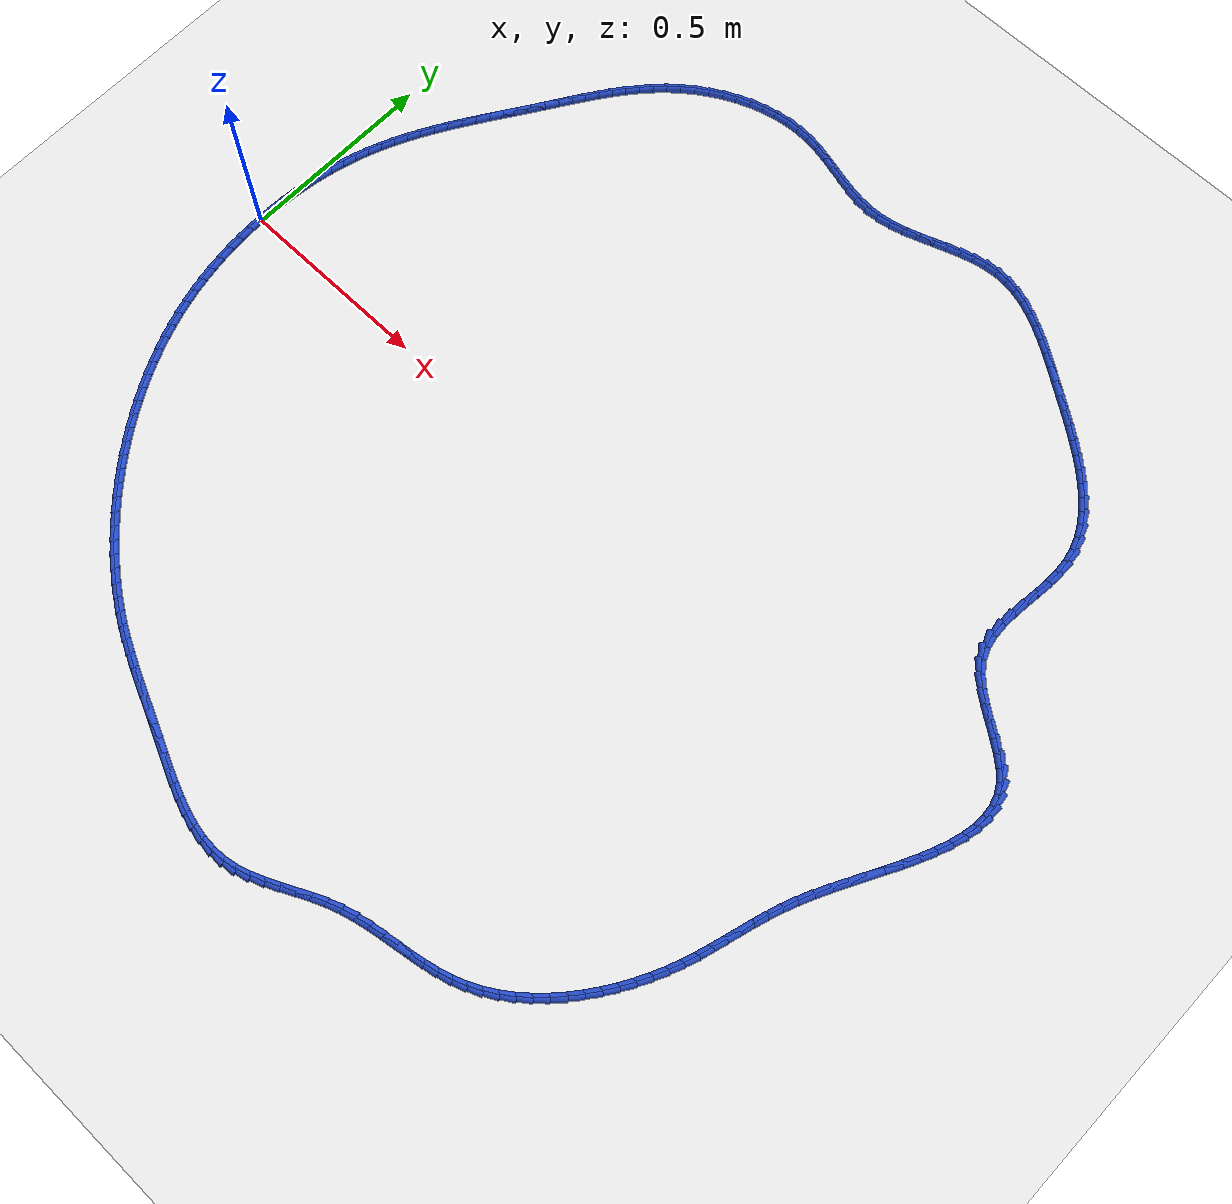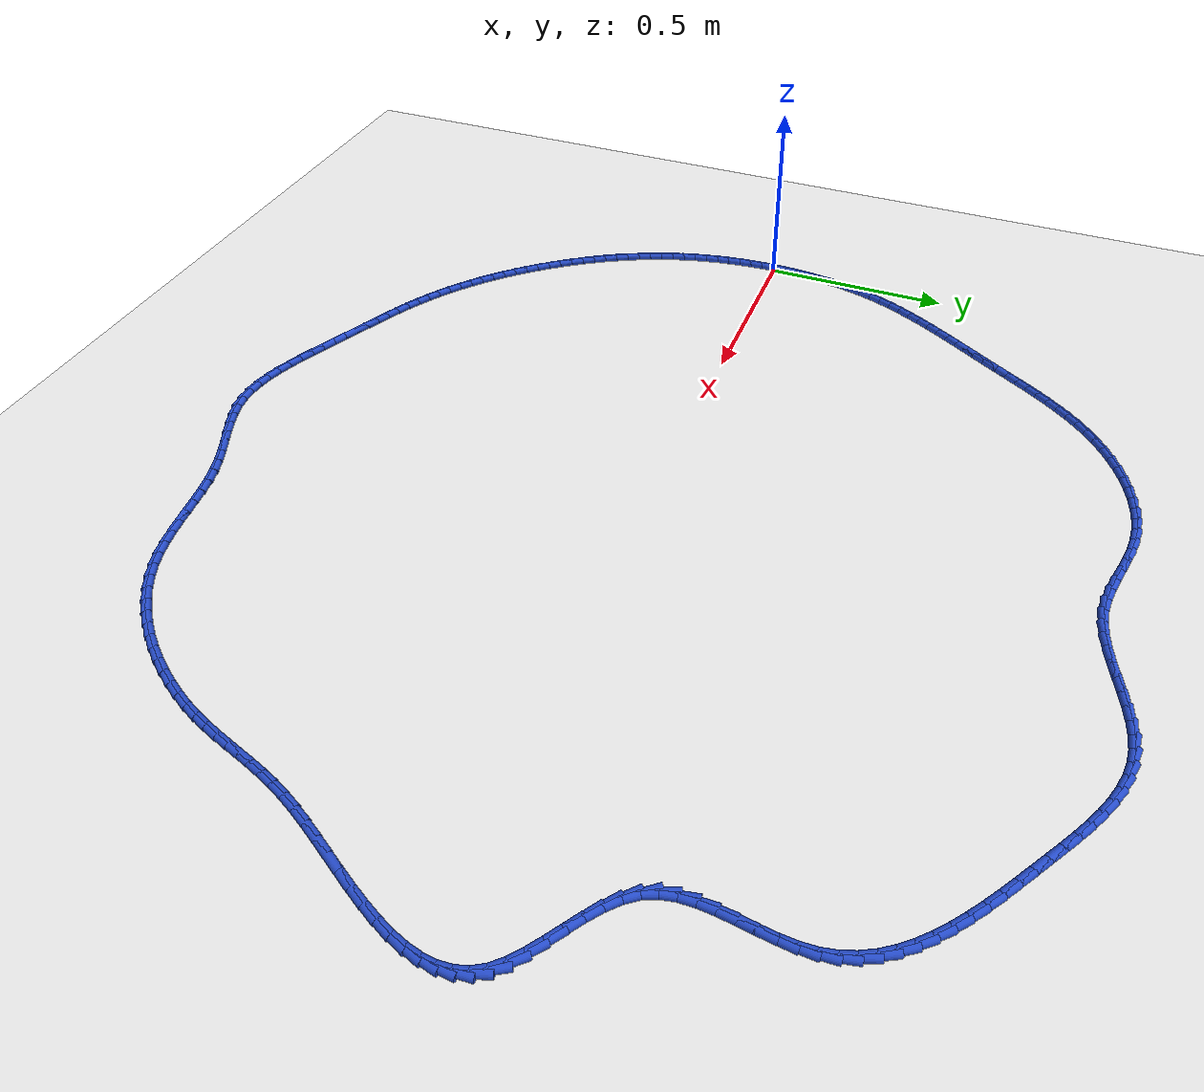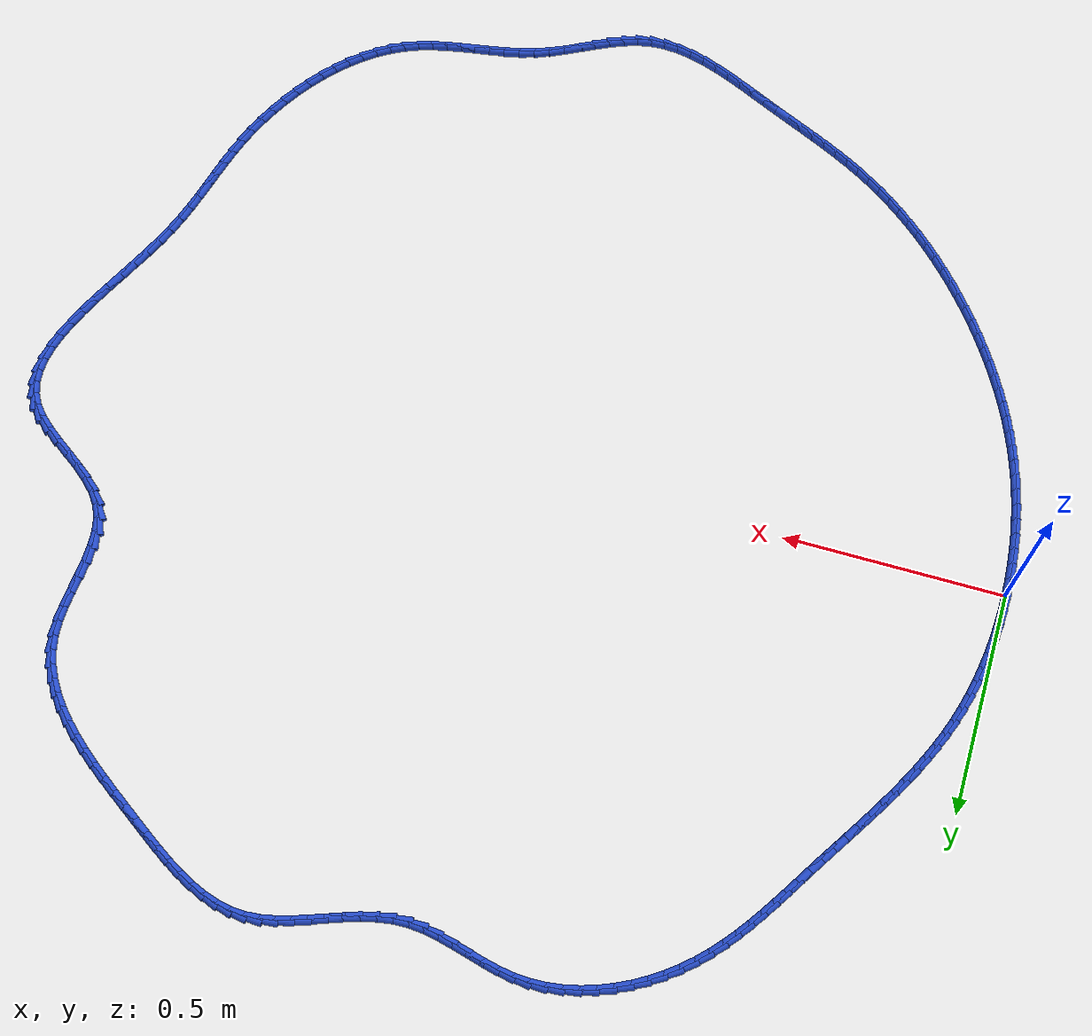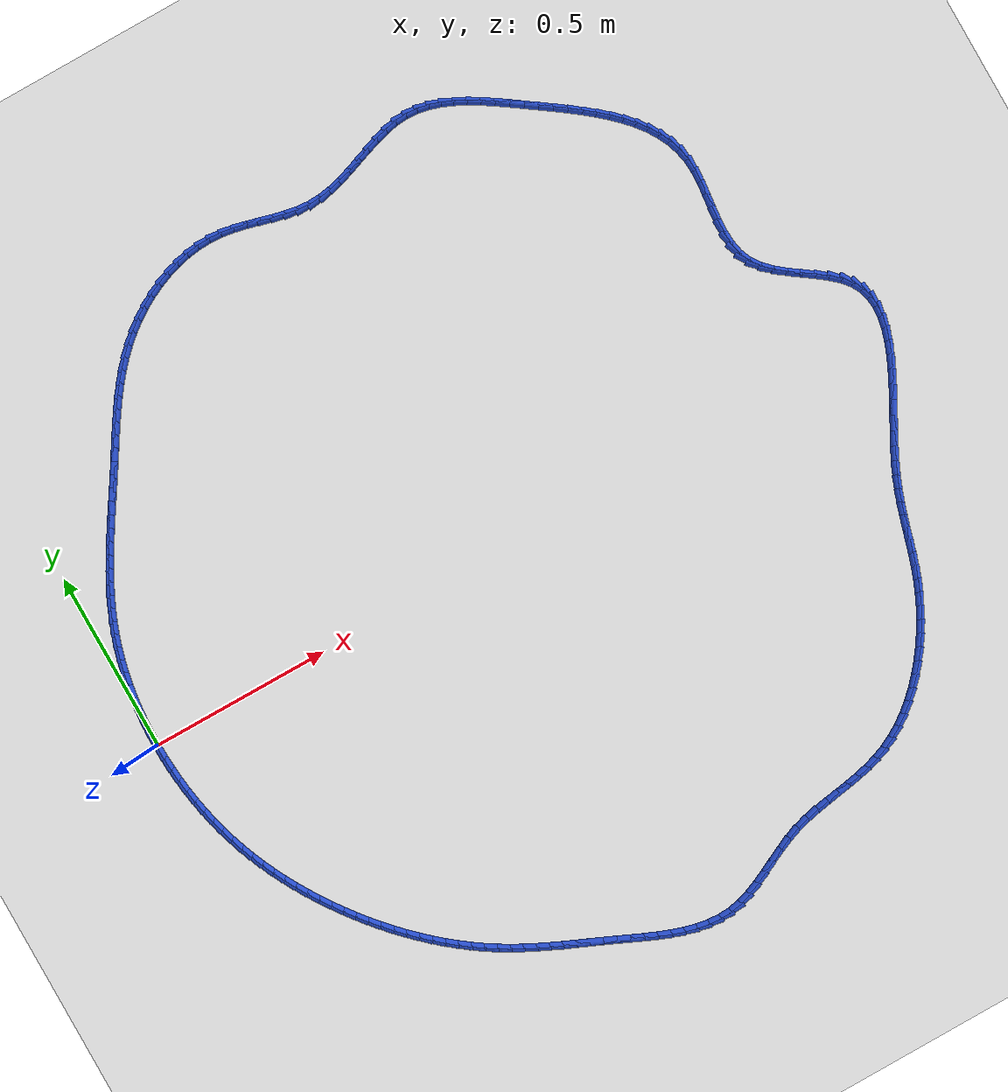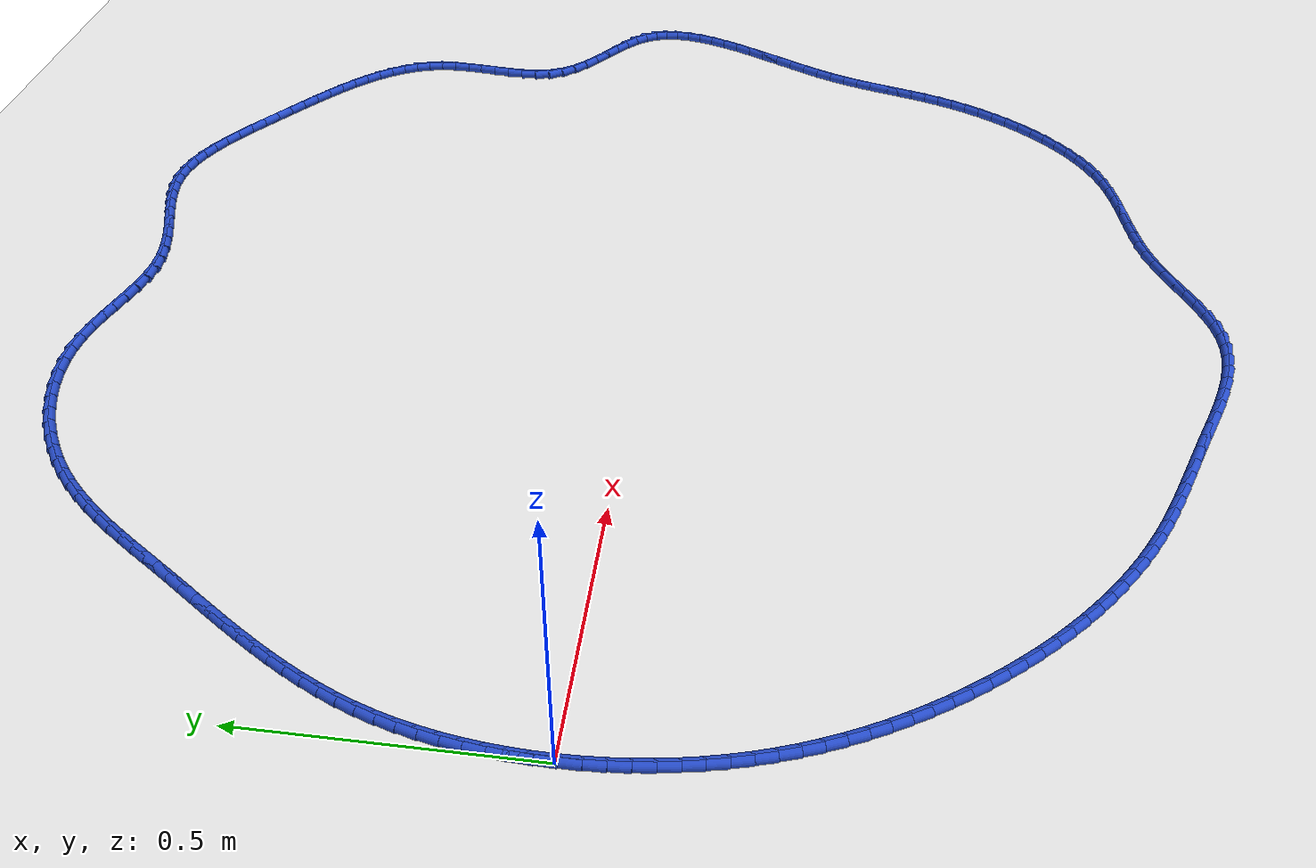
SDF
<sdf version="1.6">
 <world name="default">
  <light name="sun" type="directional">
   <pose>0 0 10 0 -0 0</pose>
   <diffuse>0.8 0.8 0.8 1</diffuse>
   <specular>0.2 0.2 0.2 1</specular>
   <attenuation>
    <range>1000</range>
    <constant>0.9</constant>
    <linear>0.01</linear>
    <quadratic>0.001</quadratic>
   </attenuation>
   <direction>-0.5 0.1 -0.9</direction>
  </light>
  <model name="ground_plane">
   <static>1</static>
   <link name="link">
    <collision name="collision">
     <geometry><plane><normal>0 0 1</normal><size>100 100</size></plane></geometry>
     <surface><friction><ode><mu>100</mu><mu2>50</mu2></ode></friction></surface>
    </collision>
    <visual name="visual">
     <cast_shadows>0</cast_shadows>
     <geometry><plane><normal>0 0 1</normal><size>100 100</size></plane></geometry>
     <material>
      <script><uri>file://media/materials/scripts/gazebo.material</uri><name>Gazebo/WhiteGlow</name></script>
     </material>
    </visual>
   </link>
  </model>
  <gravity>0 0 -9.8</gravity>
  <magnetic_field>6e-06 2.3e-05 -4.2e-05</magnetic_field>
  <atmosphere type="adiabatic"/>
  <physics name="default_physics" default="0" type="ode">
   <max_step_size>0.001</max_step_size>
   <real_time_factor>1</real_time_factor>
   <real_time_update_rate>1000</real_time_update_rate>
  </physics>
  <scene><ambient>0.4 0.4 0.4 1</ambient><background>0.7 0.7 0.7 1</background><shadows>1</shadows></scene>
  <spherical_coordinates>
   <surface_model>EARTH_WGS84</surface_model>
   <latitude_deg>0</latitude_deg>
   <longitude_deg>0</longitude_deg>
   <elevation>0</elevation>
   <heading_deg>0</heading_deg>
  </spherical_coordinates>
  <model name="line">
   <link name="link_0">
    <pose>-2.42861286636753e-17 -3.469446951953614e-17 0.01 0 1.57 1.558813016870988</pose>
    <collision name="collision">
     <geometry><cylinder><radius>0.01</radius><length>0.08</length></cylinder></geometry>
    </collision>
    <visual name="visual">
     <material>
      <script><name>Gazebo/Blue</name><uri>file://media/materials/scripts/gazebo.material</uri></script>
     </material>
     <geometry><cylinder><radius>0.01</radius><length>0.08</length></cylinder></geometry>
    </visual>
   </link>
   <link name="link_1">
    <pose>0.00041849453326578585 0.0349214452294439 0.01 0 1.57 1.5253494940375614</pose>
    <collision name="collision">
     <geometry><cylinder><radius>0.01</radius><length>0.08</length></cylinder></geometry>
    </collision>
    <visual name="visual">
     <material>
      <script><name>Gazebo/Blue</name><uri>file://media/materials/scripts/gazebo.material</uri></script>
     </material>
     <geometry><cylinder><radius>0.01</radius><length>0.08</length></cylinder></geometry>
    </visual>
   </link>
   <link name="link_2">
    <pose>0.0020054214623804953 0.06981571900852142 0.01 0 1.57 1.4909088446430492</pose>
    <collision name="collision">
     <geometry><cylinder><radius>0.01</radius><length>0.08</length></cylinder></geometry>
    </collision>
    <visual name="visual">
     <material>
      <script><name>Gazebo/Blue</name><uri>file://media/materials/scripts/gazebo.material</uri></script>
     </material>
     <geometry><cylinder><radius>0.01</radius><length>0.08</length></cylinder></geometry>
    </visual>
   </link>
   <link name="link_3">
    <pose>0.004791187950977258 0.10461263121228428 0.01 0 1.57 1.4553692420791737</pose>
    <collision name="collision">
     <geometry><cylinder><radius>0.01</radius><length>0.08</length></cylinder></geometry>
    </collision>
    <visual name="visual">
     <material>
      <script><name>Gazebo/Blue</name><uri>file://media/materials/scripts/gazebo.material</uri></script>
     </material>
     <geometry><cylinder><radius>0.01</radius><length>0.08</length></cylinder></geometry>
    </visual>
   </link>
   <link name="link_4">
    <pose>0.00880620116268925 0.13924199171578444 0.01 0 1.57 1.4186114789655588</pose>
    <collision name="collision">
     <geometry><cylinder><radius>0.01</radius><length>0.08</length></cylinder></geometry>
    </collision>
    <visual name="visual">
     <material>
      <script><name>Gazebo/Blue</name><uri>file://media/materials/scripts/gazebo.material</uri></script>
     </material>
     <geometry><cylinder><radius>0.01</radius><length>0.08</length></cylinder></geometry>
    </visual>
   </link>
   <link name="link_5">
    <pose>0.014080868261149626 0.1736336103940736 0.01 0 1.57 1.3805202278129747</pose>
    <collision name="collision">
     <geometry><cylinder><radius>0.01</radius><length>0.08</length></cylinder></geometry>
    </collision>
    <visual name="visual">
     <material>
      <script><name>Gazebo/Blue</name><uri>file://media/materials/scripts/gazebo.material</uri></script>
     </material>
     <geometry><cylinder><radius>0.01</radius><length>0.08</length></cylinder></geometry>
    </visual>
   </link>
   <link name="link_6">
    <pose>0.02064559640999155 0.2077172971222037 0.01 0 1.57 1.3409858493786462</pose>
    <collision name="collision">
     <geometry><cylinder><radius>0.01</radius><length>0.08</length></cylinder></geometry>
    </collision>
    <visual name="visual">
     <material>
      <script><name>Gazebo/Blue</name><uri>file://media/materials/scripts/gazebo.material</uri></script>
     </material>
     <geometry><cylinder><radius>0.01</radius><length>0.08</length></cylinder></geometry>
    </visual>
   </link>
   <link name="link_7">
    <pose>0.0285307927728482 0.24142286177522657 0.01 0 1.57 1.2999068125460977</pose>
    <collision name="collision">
     <geometry><cylinder><radius>0.01</radius><length>0.08</length></cylinder></geometry>
    </collision>
    <visual name="visual">
     <material>
      <script><name>Gazebo/Blue</name><uri>file://media/materials/scripts/gazebo.material</uri></script>
     </material>
     <geometry><cylinder><radius>0.01</radius><length>0.08</length></cylinder></geometry>
    </visual>
   </link>
   <link name="link_8">
    <pose>0.03776686451335271 0.27468011422819394 0.01 0 1.57 1.2571927750422107</pose>
    <collision name="collision">
     <geometry><cylinder><radius>0.01</radius><length>0.08</length></cylinder></geometry>
    </collision>
    <visual name="visual">
     <material>
      <script><name>Gazebo/Blue</name><uri>file://media/materials/scripts/gazebo.material</uri></script>
     </material>
     <geometry><cylinder><radius>0.01</radius><length>0.08</length></cylinder></geometry>
    </visual>
   </link>
   <link name="link_9">
    <pose>0.048384218795138274 0.30741886435615773 0.01 0 1.57 1.2135847178669845</pose>
    <collision name="collision">
     <geometry><cylinder><radius>0.01</radius><length>0.08</length></cylinder></geometry>
    </collision>
    <visual name="visual">
     <material>
      <script><name>Gazebo/Blue</name><uri>file://media/materials/scripts/gazebo.material</uri></script>
     </material>
     <geometry><cylinder><radius>0.01</radius><length>0.08</length></cylinder></geometry>
    </visual>
   </link>
   <link name="link_10">
    <pose>0.060390142191742345 0.3395871175885453 0.01 0 1.57 1.1729028141526583</pose>
    <collision name="collision">
     <geometry><cylinder><radius>0.01</radius><length>0.08</length></cylinder></geometry>
    </collision>
    <visual name="visual">
     <material>
      <script><name>Gazebo/Blue</name><uri>file://media/materials/scripts/gazebo.material</uri></script>
     </material>
     <geometry><cylinder><radius>0.01</radius><length>0.08</length></cylinder></geometry>
    </visual>
   </link>
   <link name="link_11">
    <pose>0.0736846875532542 0.3712172706716929 0.01 0 1.57 1.1363858791967936</pose>
    <collision name="collision">
     <geometry><cylinder><radius>0.01</radius><length>0.08</length></cylinder></geometry>
    </collision>
    <visual name="visual">
     <material>
      <script><name>Gazebo/Blue</name><uri>file://media/materials/scripts/gazebo.material</uri></script>
     </material>
     <geometry><cylinder><radius>0.01</radius><length>0.08</length></cylinder></geometry>
    </visual>
   </link>
   <link name="link_12">
    <pose>0.08813684155119664 0.4023661689641478 0.01 0 1.57 1.1041198999825512</pose>
    <collision name="collision">
     <geometry><cylinder><radius>0.01</radius><length>0.08</length></cylinder></geometry>
    </collision>
    <visual name="visual">
     <material>
      <script><name>Gazebo/Blue</name><uri>file://media/materials/scripts/gazebo.material</uri></script>
     </material>
     <geometry><cylinder><radius>0.01</radius><length>0.08</length></cylinder></geometry>
    </visual>
   </link>
   <link name="link_13">
    <pose>0.10361558764086587 0.4330906603555794 0.01 0 1.57 1.0761330196046222</pose>
    <collision name="collision">
     <geometry><cylinder><radius>0.01</radius><length>0.08</length></cylinder></geometry>
    </collision>
    <visual name="visual">
     <material>
      <script><name>Gazebo/Blue</name><uri>file://media/materials/scripts/gazebo.material</uri></script>
     </material>
     <geometry><cylinder><radius>0.01</radius><length>0.08</length></cylinder></geometry>
    </visual>
   </link>
   <link name="link_14">
    <pose>0.11998990927755801 0.463447592735657 0.01 0 1.57 1.0524129822972674</pose>
    <collision name="collision">
     <geometry><cylinder><radius>0.01</radius><length>0.08</length></cylinder></geometry>
    </collision>
    <visual name="visual">
     <material>
      <script><name>Gazebo/Blue</name><uri>file://media/materials/scripts/gazebo.material</uri></script>
     </material>
     <geometry><cylinder><radius>0.01</radius><length>0.08</length></cylinder></geometry>
    </visual>
   </link>
   <link name="link_15">
    <pose>0.13712878991656907 0.49349381399404924 0.01 0 1.57 1.032922604050618</pose>
    <collision name="collision">
     <geometry><cylinder><radius>0.01</radius><length>0.08</length></cylinder></geometry>
    </collision>
    <visual name="visual">
     <material>
      <script><name>Gazebo/Blue</name><uri>file://media/materials/scripts/gazebo.material</uri></script>
     </material>
     <geometry><cylinder><radius>0.01</radius><length>0.08</length></cylinder></geometry>
    </visual>
   </link>
   <link name="link_16">
    <pose>0.15490121301319543 0.5232861720204258 0.01 0 1.57 1.0176127412670954</pose>
    <collision name="collision">
     <geometry><cylinder><radius>0.01</radius><length>0.08</length></cylinder></geometry>
    </collision>
    <visual name="visual">
     <material>
      <script><name>Gazebo/Blue</name><uri>file://media/materials/scripts/gazebo.material</uri></script>
     </material>
     <geometry><cylinder><radius>0.01</radius><length>0.08</length></cylinder></geometry>
    </visual>
   </link>
   <link name="link_17">
    <pose>0.1731761620227331 0.5528815147044558 0.01 0 1.57 1.0064325799901488</pose>
    <collision name="collision">
     <geometry><cylinder><radius>0.01</radius><length>0.08</length></cylinder></geometry>
    </collision>
    <visual name="visual">
     <material>
      <script><name>Gazebo/Blue</name><uri>file://media/materials/scripts/gazebo.material</uri></script>
     </material>
     <geometry><cylinder><radius>0.01</radius><length>0.08</length></cylinder></geometry>
    </visual>
   </link>
   <link name="link_18">
    <pose>0.19182262040047812 0.5823366899358082 0.01 0 1.57 0.9993373445620372</pose>
    <collision name="collision">
     <geometry><cylinder><radius>0.01</radius><length>0.08</length></cylinder></geometry>
    </collision>
    <visual name="visual">
     <material>
      <script><name>Gazebo/Blue</name><uri>file://media/materials/scripts/gazebo.material</uri></script>
     </material>
     <geometry><cylinder><radius>0.01</radius><length>0.08</length></cylinder></geometry>
    </visual>
   </link>
   <link name="link_19">
    <pose>0.2107095716017268 0.6117085456041523 0.01 0 1.57 0.9962936485879014</pose>
    <collision name="collision">
     <geometry><cylinder><radius>0.01</radius><length>0.08</length></cylinder></geometry>
    </collision>
    <visual name="visual">
     <material>
      <script><name>Gazebo/Blue</name><uri>file://media/materials/scripts/gazebo.material</uri></script>
     </material>
     <geometry><cylinder><radius>0.01</radius><length>0.08</length></cylinder></geometry>
    </visual>
   </link>
   <link name="link_20">
    <pose>0.22970599908177525 0.6410539295991576 0.01 0 1.57 0.9972827271291723</pose>
    <collision name="collision">
     <geometry><cylinder><radius>0.01</radius><length>0.08</length></cylinder></geometry>
    </collision>
    <visual name="visual">
     <material>
      <script><name>Gazebo/Blue</name><uri>file://media/materials/scripts/gazebo.material</uri></script>
     </material>
     <geometry><cylinder><radius>0.01</radius><length>0.08</length></cylinder></geometry>
    </visual>
   </link>
   <link name="link_21">
    <pose>0.24868088629591947 0.6704296898104926 0.01 0 1.57 1.0022805484174506</pose>
    <collision name="collision">
     <geometry><cylinder><radius>0.01</radius><length>0.08</length></cylinder></geometry>
    </collision>
    <visual name="visual">
     <material>
      <script><name>Gazebo/Blue</name><uri>file://media/materials/scripts/gazebo.material</uri></script>
     </material>
     <geometry><cylinder><radius>0.01</radius><length>0.08</length></cylinder></geometry>
    </visual>
   </link>
   <link name="link_22">
    <pose>0.26750384115414266 0.6998922755772916 0.01 0 1.57 1.0078490235096111</pose>
    <collision name="collision">
     <geometry><cylinder><radius>0.01</radius><length>0.08</length></cylinder></geometry>
    </collision>
    <visual name="visual">
     <material>
      <script><name>Gazebo/Blue</name><uri>file://media/materials/scripts/gazebo.material</uri></script>
     </material>
     <geometry><cylinder><radius>0.01</radius><length>0.08</length></cylinder></geometry>
    </visual>
   </link>
   <link name="link_23">
    <pose>0.28614607845390094 0.7294332868904965 0.01 0 1.57 1.0067495019673958</pose>
    <collision name="collision">
     <geometry><cylinder><radius>0.01</radius><length>0.08</length></cylinder></geometry>
    </collision>
    <visual name="visual">
     <material>
      <script><name>Gazebo/Blue</name><uri>file://media/materials/scripts/gazebo.material</uri></script>
     </material>
     <geometry><cylinder><radius>0.01</radius><length>0.08</length></cylinder></geometry>
    </visual>
   </link>
   <link name="link_24">
    <pose>0.30479199109993504 0.7589082654319145 0.01 0 1.57 0.9980333671314894</pose>
    <collision name="collision">
     <geometry><cylinder><radius>0.01</radius><length>0.08</length></cylinder></geometry>
    </collision>
    <visual name="visual">
     <material>
      <script><name>Gazebo/Blue</name><uri>file://media/materials/scripts/gazebo.material</uri></script>
     </material>
     <geometry><cylinder><radius>0.01</radius><length>0.08</length></cylinder></geometry>
    </visual>
   </link>
   <link name="link_25">
    <pose>0.32365283099437797 0.7881556104580976 0.01 0 1.57 0.981636412650036</pose>
    <collision name="collision">
     <geometry><cylinder><radius>0.01</radius><length>0.08</length></cylinder></geometry>
    </collision>
    <visual name="visual">
     <material>
      <script><name>Gazebo/Blue</name><uri>file://media/materials/scripts/gazebo.material</uri></script>
     </material>
     <geometry><cylinder><radius>0.01</radius><length>0.08</length></cylinder></geometry>
    </visual>
   </link>
   <link name="link_26">
    <pose>0.342939850039362 0.8170137212255977 0.01 0 1.57 0.9574823043226727</pose>
    <collision name="collision">
     <geometry><cylinder><radius>0.01</radius><length>0.08</length></cylinder></geometry>
    </collision>
    <visual name="visual">
     <material>
      <script><name>Gazebo/Blue</name><uri>file://media/materials/scripts/gazebo.material</uri></script>
     </material>
     <geometry><cylinder><radius>0.01</radius><length>0.08</length></cylinder></geometry>
    </visual>
   </link>
   <link name="link_27">
    <pose>0.3628643001370203 0.8453209969909671 0.01 0 1.57 0.9255116972324932</pose>
    <collision name="collision">
     <geometry><cylinder><radius>0.01</radius><length>0.08</length></cylinder></geometry>
    </collision>
    <visual name="visual">
     <material>
      <script><name>Gazebo/Blue</name><uri>file://media/materials/scripts/gazebo.material</uri></script>
     </material>
     <geometry><cylinder><radius>0.01</radius><length>0.08</length></cylinder></geometry>
    </visual>
   </link>
   <link name="link_28">
    <pose>0.3836374331894852 0.872915837010757 0.01 0 1.57 0.8857264147468928</pose>
    <collision name="collision">
     <geometry><cylinder><radius>0.01</radius><length>0.08</length></cylinder></geometry>
    </collision>
    <visual name="visual">
     <material>
      <script><name>Gazebo/Blue</name><uri>file://media/materials/scripts/gazebo.material</uri></script>
     </material>
     <geometry><cylinder><radius>0.01</radius><length>0.08</length></cylinder></geometry>
    </visual>
   </link>
   <link name="link_29">
    <pose>0.4054705010988892 0.8996366405415197 0.01 0 1.57 0.8382479046032365</pose>
    <collision name="collision">
     <geometry><cylinder><radius>0.01</radius><length>0.08</length></cylinder></geometry>
    </collision>
    <visual name="visual">
     <material>
      <script><name>Gazebo/Blue</name><uri>file://media/materials/scripts/gazebo.material</uri></script>
     </material>
     <geometry><cylinder><radius>0.01</radius><length>0.08</length></cylinder></geometry>
    </visual>
   </link>
   <link name="link_30">
    <pose>0.4285747557673655 0.9253218068398074 0.01 0 1.57 0.7833856186105919</pose>
    <collision name="collision">
     <geometry><cylinder><radius>0.01</radius><length>0.08</length></cylinder></geometry>
    </collision>
    <visual name="visual">
     <material>
      <script><name>Gazebo/Blue</name><uri>file://media/materials/scripts/gazebo.material</uri></script>
     </material>
     <geometry><cylinder><radius>0.01</radius><length>0.08</length></cylinder></geometry>
    </visual>
   </link>
   <link name="link_31">
    <pose>0.45316144909704636 0.9498097351621716 0.01 0 1.57 0.7217119381056243</pose>
    <collision name="collision">
     <geometry><cylinder><radius>0.01</radius><length>0.08</length></cylinder></geometry>
    </collision>
    <visual name="visual">
     <material>
      <script><name>Gazebo/Blue</name><uri>file://media/materials/scripts/gazebo.material</uri></script>
     </material>
     <geometry><cylinder><radius>0.01</radius><length>0.08</length></cylinder></geometry>
    </visual>
   </link>
   <link name="link_32">
    <pose>0.4794414225413396 0.9729387739725748 0.01 0 1.57 0.6557624963802643</pose>
    <collision name="collision">
     <geometry><cylinder><radius>0.01</radius><length>0.08</length></cylinder></geometry>
    </collision>
    <visual name="visual">
     <material>
      <script><name>Gazebo/Blue</name><uri>file://media/materials/scripts/gazebo.material</uri></script>
     </material>
     <geometry><cylinder><radius>0.01</radius><length>0.08</length></cylinder></geometry>
    </visual>
   </link>
   <link name="link_33">
    <pose>0.5075100022224032 0.994532976836554 0.01 0 1.57 0.589482308079695</pose>
    <collision name="collision">
     <geometry><cylinder><radius>0.01</radius><length>0.08</length></cylinder></geometry>
    </collision>
    <visual name="visual">
     <material>
      <script><name>Gazebo/Blue</name><uri>file://media/materials/scripts/gazebo.material</uri></script>
     </material>
     <geometry><cylinder><radius>0.01</radius><length>0.08</length></cylinder></geometry>
    </visual>
   </link>
   <link name="link_34">
    <pose>0.5371891426423897 1.0143825678746905 0.01 0 1.57 0.5224108010826641</pose>
    <collision name="collision">
     <geometry><cylinder><radius>0.01</radius><length>0.08</length></cylinder></geometry>
    </collision>
    <visual name="visual">
     <material>
      <script><name>Gazebo/Blue</name><uri>file://media/materials/scripts/gazebo.material</uri></script>
     </material>
     <geometry><cylinder><radius>0.01</radius><length>0.08</length></cylinder></geometry>
    </visual>
   </link>
   <link name="link_35">
    <pose>0.5682612570286444 1.0322728780171904 0.01 0 1.57 0.45349003070293586</pose>
    <collision name="collision">
     <geometry><cylinder><radius>0.01</radius><length>0.08</length></cylinder></geometry>
    </collision>
    <visual name="visual">
     <material>
      <script><name>Gazebo/Blue</name><uri>file://media/materials/scripts/gazebo.material</uri></script>
     </material>
     <geometry><cylinder><radius>0.01</radius><length>0.08</length></cylinder></geometry>
    </visual>
   </link>
   <link name="link_36">
    <pose>0.6005087586085125 1.04798923819426 0.01 0 1.57 0.3816902012897755</pose>
    <collision name="collision">
     <geometry><cylinder><radius>0.01</radius><length>0.08</length></cylinder></geometry>
    </collision>
    <visual name="visual">
     <material>
      <script><name>Gazebo/Blue</name><uri>file://media/materials/scripts/gazebo.material</uri></script>
     </material>
     <geometry><cylinder><radius>0.01</radius><length>0.08</length></cylinder></geometry>
    </visual>
   </link>
   <link name="link_37">
    <pose>0.6337140606093397 1.0613169793361066 0.01 0 1.57 0.30600788919527205</pose>
    <collision name="collision">
     <geometry><cylinder><radius>0.01</radius><length>0.08</length></cylinder></geometry>
    </collision>
    <visual name="visual">
     <material>
      <script><name>Gazebo/Blue</name><uri>file://media/materials/scripts/gazebo.material</uri></script>
     </material>
     <geometry><cylinder><radius>0.01</radius><length>0.08</length></cylinder></geometry>
    </visual>
   </link>
   <link name="link_38">
    <pose>0.6676595762584705 1.0720414323729355 0.01 0 1.57 0.2254847870245804</pose>
    <collision name="collision">
     <geometry><cylinder><radius>0.01</radius><length>0.08</length></cylinder></geometry>
    </collision>
    <visual name="visual">
     <material>
      <script><name>Gazebo/Blue</name><uri>file://media/materials/scripts/gazebo.material</uri></script>
     </material>
     <geometry><cylinder><radius>0.01</radius><length>0.08</length></cylinder></geometry>
    </visual>
   </link>
   <link name="link_39">
    <pose>0.7021277187832511 1.079947928234954 0.01 0 1.57 0.13925456413899726</pose>
    <collision name="collision">
     <geometry><cylinder><radius>0.01</radius><length>0.08</length></cylinder></geometry>
    </collision>
    <visual name="visual">
     <material>
      <script><name>Gazebo/Blue</name><uri>file://media/materials/scripts/gazebo.material</uri></script>
     </material>
     <geometry><cylinder><radius>0.01</radius><length>0.08</length></cylinder></geometry>
    </visual>
   </link>
   <link name="link_40">
    <pose>0.7369009014110264 1.0848217978523687 0.01 0 1.57 0.046625524637756446</pose>
    <collision name="collision">
     <geometry><cylinder><radius>0.01</radius><length>0.08</length></cylinder></geometry>
    </collision>
    <visual name="visual">
     <material>
      <script><name>Gazebo/Blue</name><uri>file://media/materials/scripts/gazebo.material</uri></script>
     </material>
     <geometry><cylinder><radius>0.01</radius><length>0.08</length></cylinder></geometry>
    </visual>
   </link>
   <link name="link_41">
    <pose>0.7717615373691418 1.0864483721553855 0.01 0 1.57 -0.05277712604272131</pose>
    <collision name="collision">
     <geometry><cylinder><radius>0.01</radius><length>0.08</length></cylinder></geometry>
    </collision>
    <visual name="visual">
     <material>
      <script><name>Gazebo/Blue</name><uri>file://media/materials/scripts/gazebo.material</uri></script>
     </material>
     <geometry><cylinder><radius>0.01</radius><length>0.08</length></cylinder></geometry>
    </visual>
   </link>
   <link name="link_42">
    <pose>0.8064921868336514 1.084613684513014 0.01 0 1.57 -0.14932525937800892</pose>
    <collision name="collision">
     <geometry><cylinder><radius>0.01</radius><length>0.08</length></cylinder></geometry>
    </collision>
    <visual name="visual">
     <material>
      <script><name>Gazebo/Blue</name><uri>file://media/materials/scripts/gazebo.material</uri></script>
     </material>
     <geometry><cylinder><radius>0.01</radius><length>0.08</length></cylinder></geometry>
    </visual>
   </link>
   <link name="link_43">
    <pose>0.8409437844163282 1.0794306092507233 0.01 0 1.57 -0.21790726805308258</pose>
    <collision name="collision">
     <geometry><cylinder><radius>0.01</radius><length>0.08</length></cylinder></geometry>
    </collision>
    <visual name="visual">
     <material>
      <script><name>Gazebo/Blue</name><uri>file://media/materials/scripts/gazebo.material</uri></script>
     </material>
     <geometry><cylinder><radius>0.01</radius><length>0.08</length></cylinder></geometry>
    </visual>
   </link>
   <link name="link_44">
    <pose>0.8751442096425758 1.0718578462456734 0.01 0 1.57 -0.2551209355972846</pose>
    <collision name="collision">
     <geometry><cylinder><radius>0.01</radius><length>0.08</length></cylinder></geometry>
    </collision>
    <visual name="visual">
     <material>
      <script><name>Gazebo/Blue</name><uri>file://media/materials/scripts/gazebo.material</uri></script>
     </material>
     <geometry><cylinder><radius>0.01</radius><length>0.08</length></cylinder></geometry>
    </visual>
   </link>
   <link name="link_45">
    <pose>0.9091495868651253 1.06298911025715 0.01 0 1.57 -0.26170310792898993</pose>
    <collision name="collision">
     <geometry><cylinder><radius>0.01</radius><length>0.08</length></cylinder></geometry>
    </collision>
    <visual name="visual">
     <material>
      <script><name>Gazebo/Blue</name><uri>file://media/materials/scripts/gazebo.material</uri></script>
     </material>
     <geometry><cylinder><radius>0.01</radius><length>0.08</length></cylinder></geometry>
    </visual>
   </link>
   <link name="link_46">
    <pose>0.9430160404367084 1.0539181160444395 0.01 0 1.57 -0.23754405952323146</pose>
    <collision name="collision">
     <geometry><cylinder><radius>0.01</radius><length>0.08</length></cylinder></geometry>
    </collision>
    <visual name="visual">
     <material>
      <script><name>Gazebo/Blue</name><uri>file://media/materials/scripts/gazebo.material</uri></script>
     </material>
     <geometry><cylinder><radius>0.01</radius><length>0.08</length></cylinder></geometry>
    </visual>
   </link>
   <link name="link_47">
    <pose>0.9767996947100561 1.0457385783668263 0.01 0 1.57 -0.18147988965904932</pose>
    <collision name="collision">
     <geometry><cylinder><radius>0.01</radius><length>0.08</length></cylinder></geometry>
    </collision>
    <visual name="visual">
     <material>
      <script><name>Gazebo/Blue</name><uri>file://media/materials/scripts/gazebo.material</uri></script>
     </material>
     <geometry><cylinder><radius>0.01</radius><length>0.08</length></cylinder></geometry>
    </visual>
   </link>
   <link name="link_48">
    <pose>1.0105566740379 1.0395442119835967 0.01 0 1.57 -0.0919509711508859</pose>
    <collision name="collision">
     <geometry><cylinder><radius>0.01</radius><length>0.08</length></cylinder></geometry>
    </collision>
    <visual name="visual">
     <material>
      <script><name>Gazebo/Blue</name><uri>file://media/materials/scripts/gazebo.material</uri></script>
     </material>
     <geometry><cylinder><radius>0.01</radius><length>0.08</length></cylinder></geometry>
    </visual>
   </link>
   <link name="link_49">
    <pose>1.0443431027729708 1.0364287316540364 0.01 0 1.57 0.029942029799785563</pose>
    <collision name="collision">
     <geometry><cylinder><radius>0.01</radius><length>0.08</length></cylinder></geometry>
    </collision>
    <visual name="visual">
     <material>
      <script><name>Gazebo/Blue</name><uri>file://media/materials/scripts/gazebo.material</uri></script>
     </material>
     <geometry><cylinder><radius>0.01</radius><length>0.08</length></cylinder></geometry>
    </visual>
   </link>
   <link name="link_50">
    <pose>1.0782127935245418 1.0374431621160902 0.01 0 1.57 0.15181166804911284</pose>
    <collision name="collision">
     <geometry><cylinder><radius>0.01</radius><length>0.08</length></cylinder></geometry>
    </collision>
    <visual name="visual">
     <material>
      <script><name>Gazebo/Blue</name><uri>file://media/materials/scripts/gazebo.material</uri></script>
     </material>
     <geometry><cylinder><radius>0.01</radius><length>0.08</length></cylinder></geometry>
    </visual>
   </link>
   <link name="link_51">
    <pose>1.1121653526071058 1.0426375226234637 0.01 0 1.57 0.24269217356533637</pose>
    <collision name="collision">
     <geometry><cylinder><radius>0.01</radius><length>0.08</length></cylinder></geometry>
    </collision>
    <visual name="visual">
     <material>
      <script><name>Gazebo/Blue</name><uri>file://media/materials/scripts/gazebo.material</uri></script>
     </material>
     <geometry><cylinder><radius>0.01</radius><length>0.08</length></cylinder></geometry>
    </visual>
   </link>
   <link name="link_52">
    <pose>1.1461455980494946 1.0510500795578759 0.01 0 1.57 0.3032794079751414</pose>
    <collision name="collision">
     <geometry><cylinder><radius>0.01</radius><length>0.08</length></cylinder></geometry>
    </collision>
    <visual name="visual">
     <material>
      <script><name>Gazebo/Blue</name><uri>file://media/materials/scripts/gazebo.material</uri></script>
     </material>
     <geometry><cylinder><radius>0.01</radius><length>0.08</length></cylinder></geometry>
    </visual>
   </link>
   <link name="link_53">
    <pose>1.1800959197347394 1.0616742597253073 0.01 0 1.57 0.33607630048696785</pose>
    <collision name="collision">
     <geometry><cylinder><radius>0.01</radius><length>0.08</length></cylinder></geometry>
    </collision>
    <visual name="visual">
     <material>
      <script><name>Gazebo/Blue</name><uri>file://media/materials/scripts/gazebo.material</uri></script>
     </material>
     <geometry><cylinder><radius>0.01</radius><length>0.08</length></cylinder></geometry>
    </visual>
   </link>
   <link name="link_54">
    <pose>1.2139587075458738 1.073503489931738 0.01 0 1.57 0.3426475296527716</pose>
    <collision name="collision">
     <geometry><cylinder><radius>0.01</radius><length>0.08</length></cylinder></geometry>
    </collision>
    <visual name="visual">
     <material>
      <script><name>Gazebo/Blue</name><uri>file://media/materials/scripts/gazebo.material</uri></script>
     </material>
     <geometry><cylinder><radius>0.01</radius><length>0.08</length></cylinder></geometry>
    </visual>
   </link>
   <link name="link_55">
    <pose>1.2476763513659295 1.0855311969831476 0.01 0 1.57 0.3230384642343847</pose>
    <collision name="collision">
     <geometry><cylinder><radius>0.01</radius><length>0.08</length></cylinder></geometry>
    </collision>
    <visual name="visual">
     <material>
      <script><name>Gazebo/Blue</name><uri>file://media/materials/scripts/gazebo.material</uri></script>
     </material>
     <geometry><cylinder><radius>0.01</radius><length>0.08</length></cylinder></geometry>
    </visual>
   </link>
   <link name="link_56">
    <pose>1.2811912410779394 1.096750807685517 0.01 0 1.57 0.275618880519593</pose>
    <collision name="collision">
     <geometry><cylinder><radius>0.01</radius><length>0.08</length></cylinder></geometry>
    </collision>
    <visual name="visual">
     <material>
      <script><name>Gazebo/Blue</name><uri>file://media/materials/scripts/gazebo.material</uri></script>
     </material>
     <geometry><cylinder><radius>0.01</radius><length>0.08</length></cylinder></geometry>
    </visual>
   </link>
   <link name="link_57">
    <pose>1.314445766564936 1.1061557488448261 0.01 0 1.57 0.1972901157692355</pose>
    <collision name="collision">
     <geometry><cylinder><radius>0.01</radius><length>0.08</length></cylinder></geometry>
    </collision>
    <visual name="visual">
     <material>
      <script><name>Gazebo/Blue</name><uri>file://media/materials/scripts/gazebo.material</uri></script>
     </material>
     <geometry><cylinder><radius>0.01</radius><length>0.08</length></cylinder></geometry>
    </visual>
   </link>
   <link name="link_58">
    <pose>1.3473823177099518 1.1127394472670553 0.01 0 1.57 0.08443658635671142</pose>
    <collision name="collision">
     <geometry><cylinder><radius>0.01</radius><length>0.08</length></cylinder></geometry>
    </collision>
    <visual name="visual">
     <material>
      <script><name>Gazebo/Blue</name><uri>file://media/materials/scripts/gazebo.material</uri></script>
     </material>
     <geometry><cylinder><radius>0.01</radius><length>0.08</length></cylinder></geometry>
    </visual>
   </link>
   <link name="link_59">
    <pose>1.3799432849909703 1.115495336713165 0.01 0 1.57 -0.056012142532051674</pose>
    <collision name="collision">
     <geometry><cylinder><radius>0.01</radius><length>0.08</length></cylinder></geometry>
    </collision>
    <visual name="visual">
     <material>
      <script><name>Gazebo/Blue</name><uri>file://media/materials/scripts/gazebo.material</uri></script>
     </material>
     <geometry><cylinder><radius>0.01</radius><length>0.08</length></cylinder></geometry>
    </visual>
   </link>
   <link name="link_60">
    <pose>1.4120946459859458 1.113692584409685 0.01 0 1.57 -0.18909500730641726</pose>
    <collision name="collision">
     <geometry><cylinder><radius>0.01</radius><length>0.08</length></cylinder></geometry>
    </collision>
    <visual name="visual">
     <material>
      <script><name>Gazebo/Blue</name><uri>file://media/materials/scripts/gazebo.material</uri></script>
     </material>
     <geometry><cylinder><radius>0.01</radius><length>0.08</length></cylinder></geometry>
    </visual>
   </link>
   <link name="link_61">
    <pose>1.443888559443866 1.1076078164477157 0.01 0 1.57 -0.30328335693526753</pose>
    <collision name="collision">
     <geometry><cylinder><radius>0.01</radius><length>0.08</length></cylinder></geometry>
    </collision>
    <visual name="visual">
     <material>
      <script><name>Gazebo/Blue</name><uri>file://media/materials/scripts/gazebo.material</uri></script>
     </material>
     <geometry><cylinder><radius>0.01</radius><length>0.08</length></cylinder></geometry>
    </visual>
   </link>
   <link name="link_62">
    <pose>1.4753968615592399 1.0977476884791724 0.01 0 1.57 -0.39722403735083267</pose>
    <collision name="collision">
     <geometry><cylinder><radius>0.01</radius><length>0.08</length></cylinder></geometry>
    </collision>
    <visual name="visual">
     <material>
      <script><name>Gazebo/Blue</name><uri>file://media/materials/scripts/gazebo.material</uri></script>
     </material>
     <geometry><cylinder><radius>0.01</radius><length>0.08</length></cylinder></geometry>
    </visual>
   </link>
   <link name="link_63">
    <pose>1.5066913885265765 1.084618856155971 0.01 0 1.57 -0.47169354487999915</pose>
    <collision name="collision">
     <geometry><cylinder><radius>0.01</radius><length>0.08</length></cylinder></geometry>
    </collision>
    <visual name="visual">
     <material>
      <script><name>Gazebo/Blue</name><uri>file://media/materials/scripts/gazebo.material</uri></script>
     </material>
     <geometry><cylinder><radius>0.01</radius><length>0.08</length></cylinder></geometry>
    </visual>
   </link>
   <link name="link_64">
    <pose>1.5378439765403846 1.0687279751300263 0.01 0 1.57 -0.5284302229090233</pose>
    <collision name="collision">
     <geometry><cylinder><radius>0.01</radius><length>0.08</length></cylinder></geometry>
    </collision>
    <visual name="visual">
     <material>
      <script><name>Gazebo/Blue</name><uri>file://media/materials/scripts/gazebo.material</uri></script>
     </material>
     <geometry><cylinder><radius>0.01</radius><length>0.08</length></cylinder></geometry>
    </visual>
   </link>
   <link name="link_65">
    <pose>1.568926461795174 1.0505817010532537 0.01 0 1.57 -0.5693385582696825</pose>
    <collision name="collision">
     <geometry><cylinder><radius>0.01</radius><length>0.08</length></cylinder></geometry>
    </collision>
    <visual name="visual">
     <material>
      <script><name>Gazebo/Blue</name><uri>file://media/materials/scripts/gazebo.material</uri></script>
     </material>
     <geometry><cylinder><radius>0.01</radius><length>0.08</length></cylinder></geometry>
    </visual>
   </link>
   <link name="link_66">
    <pose>1.600010680485454 1.0306866895775688 0.01 0 1.57 -0.596074051037048</pose>
    <collision name="collision">
     <geometry><cylinder><radius>0.01</radius><length>0.08</length></cylinder></geometry>
    </collision>
    <visual name="visual">
     <material>
      <script><name>Gazebo/Blue</name><uri>file://media/materials/scripts/gazebo.material</uri></script>
     </material>
     <geometry><cylinder><radius>0.01</radius><length>0.08</length></cylinder></geometry>
    </visual>
   </link>
   <link name="link_67">
    <pose>1.631168468805733 1.0095495963548868 0.01 0 1.57 -0.6098739325952048</pose>
    <collision name="collision">
     <geometry><cylinder><radius>0.01</radius><length>0.08</length></cylinder></geometry>
    </collision>
    <visual name="visual">
     <material>
      <script><name>Gazebo/Blue</name><uri>file://media/materials/scripts/gazebo.material</uri></script>
     </material>
     <geometry><cylinder><radius>0.01</radius><length>0.08</length></cylinder></geometry>
    </visual>
   </link>
   <link name="link_68">
    <pose>1.6624716629505207 0.9876770770371232 0.01 0 1.57 -0.6123080314083231</pose>
    <collision name="collision">
     <geometry><cylinder><radius>0.01</radius><length>0.08</length></cylinder></geometry>
    </collision>
    <visual name="visual">
     <material>
      <script><name>Gazebo/Blue</name><uri>file://media/materials/scripts/gazebo.material</uri></script>
     </material>
     <geometry><cylinder><radius>0.01</radius><length>0.08</length></cylinder></geometry>
    </visual>
   </link>
   <link name="link_69">
    <pose>1.6939745453412336 0.9655507158599711 0.01 0 1.57 -0.6148315728116782</pose>
    <collision name="collision">
     <geometry><cylinder><radius>0.01</radius><length>0.08</length></cylinder></geometry>
    </collision>
    <visual name="visual">
     <material>
      <script><name>Gazebo/Blue</name><uri>file://media/materials/scripts/gazebo.material</uri></script>
     </material>
     <geometry><cylinder><radius>0.01</radius><length>0.08</length></cylinder></geometry>
    </visual>
   </link>
   <link name="link_70">
    <pose>1.7254849555225673 0.943300111653791 0.01 0 1.57 -0.625736549290346</pose>
    <collision name="collision">
     <geometry><cylinder><radius>0.01</radius><length>0.08</length></cylinder></geometry>
    </collision>
    <visual name="visual">
     <material>
      <script><name>Gazebo/Blue</name><uri>file://media/materials/scripts/gazebo.material</uri></script>
     </material>
     <geometry><cylinder><radius>0.01</radius><length>0.08</length></cylinder></geometry>
    </visual>
   </link>
   <link name="link_71">
    <pose>1.7566289856701462 0.9207952800862161 0.01 0 1.57 -0.6455079387296807</pose>
    <collision name="collision">
     <geometry><cylinder><radius>0.01</radius><length>0.08</length></cylinder></geometry>
    </collision>
    <visual name="visual">
     <material>
      <script><name>Gazebo/Blue</name><uri>file://media/materials/scripts/gazebo.material</uri></script>
     </material>
     <geometry><cylinder><radius>0.01</radius><length>0.08</length></cylinder></geometry>
    </visual>
   </link>
   <link name="link_72">
    <pose>1.7870284905742648 0.8979001847213931 0.01 0 1.57 -0.6747394434333985</pose>
    <collision name="collision">
     <geometry><cylinder><radius>0.01</radius><length>0.08</length></cylinder></geometry>
    </collision>
    <visual name="visual">
     <material>
      <script><name>Gazebo/Blue</name><uri>file://media/materials/scripts/gazebo.material</uri></script>
     </material>
     <geometry><cylinder><radius>0.01</radius><length>0.08</length></cylinder></geometry>
    </visual>
   </link>
   <link name="link_73">
    <pose>1.8163053250252157 0.8744787891234693 0.01 0 1.57 -0.7143205644950589</pose>
    <collision name="collision">
     <geometry><cylinder><radius>0.01</radius><length>0.08</length></cylinder></geometry>
    </collision>
    <visual name="visual">
     <material>
      <script><name>Gazebo/Blue</name><uri>file://media/materials/scripts/gazebo.material</uri></script>
     </material>
     <geometry><cylinder><radius>0.01</radius><length>0.08</length></cylinder></geometry>
    </visual>
   </link>
   <link name="link_74">
    <pose>1.844081343813294 0.8503950568565921 0.01 0 1.57 -0.7654132453417026</pose>
    <collision name="collision">
     <geometry><cylinder><radius>0.01</radius><length>0.08</length></cylinder></geometry>
    </collision>
    <visual name="visual">
     <material>
      <script><name>Gazebo/Blue</name><uri>file://media/materials/scripts/gazebo.material</uri></script>
     </material>
     <geometry><cylinder><radius>0.01</radius><length>0.08</length></cylinder></geometry>
    </visual>
   </link>
   <link name="link_75">
    <pose>1.8699784017287924 0.8255129514849087 0.01 0 1.57 -0.829379458999169</pose>
    <collision name="collision">
     <geometry><cylinder><radius>0.01</radius><length>0.08</length></cylinder></geometry>
    </collision>
    <visual name="visual">
     <material>
      <script><name>Gazebo/Blue</name><uri>file://media/materials/scripts/gazebo.material</uri></script>
     </material>
     <geometry><cylinder><radius>0.01</radius><length>0.08</length></cylinder></geometry>
    </visual>
   </link>
   <link name="link_76">
    <pose>1.8936183535620055 0.7996964365725665 0.01 0 1.57 -0.9076103711857294</pose>
    <collision name="collision">
     <geometry><cylinder><radius>0.01</radius><length>0.08</length></cylinder></geometry>
    </collision>
    <visual name="visual">
     <material>
      <script><name>Gazebo/Blue</name><uri>file://media/materials/scripts/gazebo.material</uri></script>
     </material>
     <geometry><cylinder><radius>0.01</radius><length>0.08</length></cylinder></geometry>
    </visual>
   </link>
   <link name="link_77">
    <pose>1.914623054103227 0.7728094756837127 0.01 0 1.57 -1.0011927811730217</pose>
    <collision name="collision">
     <geometry><cylinder><radius>0.01</radius><length>0.08</length></cylinder></geometry>
    </collision>
    <visual name="visual">
     <material>
      <script><name>Gazebo/Blue</name><uri>file://media/materials/scripts/gazebo.material</uri></script>
     </material>
     <geometry><cylinder><radius>0.01</radius><length>0.08</length></cylinder></geometry>
    </visual>
   </link>
   <link name="link_78">
    <pose>1.93261435814275 0.7447160323824943 0.01 0 1.57 -1.1103667829818296</pose>
    <collision name="collision">
     <geometry><cylinder><radius>0.01</radius><length>0.08</length></cylinder></geometry>
    </collision>
    <visual name="visual">
     <material>
      <script><name>Gazebo/Blue</name><uri>file://media/materials/scripts/gazebo.material</uri></script>
     </material>
     <geometry><cylinder><radius>0.01</radius><length>0.08</length></cylinder></geometry>
    </visual>
   </link>
   <link name="link_79">
    <pose>1.947214120470869 0.715280070233059 0.01 0 1.57 -1.2338335289501963</pose>
    <collision name="collision">
     <geometry><cylinder><radius>0.01</radius><length>0.08</length></cylinder></geometry>
    </collision>
    <visual name="visual">
     <material>
      <script><name>Gazebo/Blue</name><uri>file://media/materials/scripts/gazebo.material</uri></script>
     </material>
     <geometry><cylinder><radius>0.01</radius><length>0.08</length></cylinder></geometry>
    </visual>
   </link>
   <link name="link_80">
    <pose>1.9580441958778771 0.6843655527995535 0.01 0 1.57 -1.3681913488515838</pose>
    <collision name="collision">
     <geometry><cylinder><radius>0.01</radius><length>0.08</length></cylinder></geometry>
    </collision>
    <visual name="visual">
     <material>
      <script><name>Gazebo/Blue</name><uri>file://media/materials/scripts/gazebo.material</uri></script>
     </material>
     <geometry><cylinder><radius>0.01</radius><length>0.08</length></cylinder></geometry>
    </visual>
   </link>
   <link name="link_81">
    <pose>1.9647264391540689 0.6518364436461254 0.01 0 1.57 -1.5033694523254097</pose>
    <collision name="collision">
     <geometry><cylinder><radius>0.01</radius><length>0.08</length></cylinder></geometry>
    </collision>
    <visual name="visual">
     <material>
      <script><name>Gazebo/Blue</name><uri>file://media/materials/scripts/gazebo.material</uri></script>
     </material>
     <geometry><cylinder><radius>0.01</radius><length>0.08</length></cylinder></geometry>
    </visual>
   </link>
   <link name="link_82">
    <pose>1.9670372302159325 0.6176173269495185 0.01 0 1.57 1.537589407826876</pose>
    <collision name="collision">
     <geometry><cylinder><radius>0.01</radius><length>0.08</length></cylinder></geometry>
    </collision>
    <visual name="visual">
     <material>
      <script><name>Gazebo/Blue</name><uri>file://media/materials/scripts/gazebo.material</uri></script>
     </material>
     <geometry><cylinder><radius>0.01</radius><length>0.08</length></cylinder></geometry>
    </visual>
   </link>
   <link name="link_83">
    <pose>1.9658562330426916 0.5820656081201379 0.01 0 1.57 1.4798669553326602</pose>
    <collision name="collision">
     <geometry><cylinder><radius>0.01</radius><length>0.08</length></cylinder></geometry>
    </collision>
    <visual name="visual">
     <material>
      <script><name>Gazebo/Blue</name><uri>file://media/materials/scripts/gazebo.material</uri></script>
     </material>
     <geometry><cylinder><radius>0.01</radius><length>0.08</length></cylinder></geometry>
    </visual>
   </link>
   <link name="link_84">
    <pose>1.9625428394228048 0.5457268910471185 0.01 0 1.57 1.4595973419241728</pose>
    <collision name="collision">
     <geometry><cylinder><radius>0.01</radius><length>0.08</length></cylinder></geometry>
    </collision>
    <visual name="visual">
     <material>
      <script><name>Gazebo/Blue</name><uri>file://media/materials/scripts/gazebo.material</uri></script>
     </material>
     <geometry><cylinder><radius>0.01</radius><length>0.08</length></cylinder></geometry>
    </visual>
   </link>
   <link name="link_85">
    <pose>1.9584584049716753 0.5091475500340599 0.01 0 1.57 1.4747657924430475</pose>
    <collision name="collision">
     <geometry><cylinder><radius>0.01</radius><length>0.08</length></cylinder></geometry>
    </collision>
    <visual name="visual">
     <material>
      <script><name>Gazebo/Blue</name><uri>file://media/materials/scripts/gazebo.material</uri></script>
     </material>
     <geometry><cylinder><radius>0.01</radius><length>0.08</length></cylinder></geometry>
    </visual>
   </link>
   <link name="link_86">
    <pose>1.9549642853047082 0.4728739593845634 0.01 0 1.57 1.5272782116818082</pose>
    <collision name="collision">
     <geometry><cylinder><radius>0.01</radius><length>0.08</length></cylinder></geometry>
    </collision>
    <visual name="visual">
     <material>
      <script><name>Gazebo/Blue</name><uri>file://media/materials/scripts/gazebo.material</uri></script>
     </material>
     <geometry><cylinder><radius>0.01</radius><length>0.08</length></cylinder></geometry>
    </visual>
   </link>
   <link name="link_87">
    <pose>1.9534218360373048 0.4374524934022286 0.01 0 1.57 -1.5188025966677123</pose>
    <collision name="collision">
     <geometry><cylinder><radius>0.01</radius><length>0.08</length></cylinder></geometry>
    </collision>
    <visual name="visual">
     <material>
      <script><name>Gazebo/Blue</name><uri>file://media/materials/scripts/gazebo.material</uri></script>
     </material>
     <geometry><cylinder><radius>0.01</radius><length>0.08</length></cylinder></geometry>
    </visual>
   </link>
   <link name="link_88">
    <pose>1.95519241278487 0.40342952639065605 0.01 0 1.57 -1.3725214686014056</pose>
    <collision name="collision">
     <geometry><cylinder><radius>0.01</radius><length>0.08</length></cylinder></geometry>
    </collision>
    <visual name="visual">
     <material>
      <script><name>Gazebo/Blue</name><uri>file://media/materials/scripts/gazebo.material</uri></script>
     </material>
     <geometry><cylinder><radius>0.01</radius><length>0.08</length></cylinder></geometry>
    </visual>
   </link>
   <link name="link_89">
    <pose>1.9616373711628081 0.37135143265344617 0.01 0 1.57 -1.1716516513190787</pose>
    <collision name="collision">
     <geometry><cylinder><radius>0.01</radius><length>0.08</length></cylinder></geometry>
    </collision>
    <visual name="visual">
     <material>
      <script><name>Gazebo/Blue</name><uri>file://media/materials/scripts/gazebo.material</uri></script>
     </material>
     <geometry><cylinder><radius>0.01</radius><length>0.08</length></cylinder></geometry>
    </visual>
   </link>
   <link name="link_90">
    <pose>1.9741168622989902 0.3417641303141009 0.01 0 1.57 -0.951187355734402</pose>
    <collision name="collision">
     <geometry><cylinder><radius>0.01</radius><length>0.08</length></cylinder></geometry>
    </collision>
    <visual name="visual">
     <material>
      <script><name>Gazebo/Blue</name><uri>file://media/materials/scripts/gazebo.material</uri></script>
     </material>
     <geometry><cylinder><radius>0.01</radius><length>0.08</length></cylinder></geometry>
    </visual>
   </link>
   <link name="link_91">
    <pose>1.9932548007412672 0.3149346998439888 0.01 0 1.57 -0.7878995629009764</pose>
    <collision name="collision">
     <geometry><cylinder><radius>0.01</radius><length>0.08</length></cylinder></geometry>
    </collision>
    <visual name="visual">
     <material>
      <script><name>Gazebo/Blue</name><uri>file://media/materials/scripts/gazebo.material</uri></script>
     </material>
     <geometry><cylinder><radius>0.01</radius><length>0.08</length></cylinder></geometry>
    </visual>
   </link>
   <link name="link_92">
    <pose>2.017688953904014 0.2903780007320945 0.01 0 1.57 -0.6847818334524841</pose>
    <collision name="collision">
     <geometry><cylinder><radius>0.01</radius><length>0.08</length></cylinder></geometry>
    </collision>
    <visual name="visual">
     <material>
      <script><name>Gazebo/Blue</name><uri>file://media/materials/scripts/gazebo.material</uri></script>
     </material>
     <geometry><cylinder><radius>0.01</radius><length>0.08</length></cylinder></geometry>
    </visual>
   </link>
   <link name="link_93">
    <pose>2.0457255180236755 0.26748331526670605 0.01 0 1.57 -0.6302163446729163</pose>
    <collision name="collision">
     <geometry><cylinder><radius>0.01</radius><length>0.08</length></cylinder></geometry>
    </collision>
    <visual name="visual">
     <material>
      <script><name>Gazebo/Blue</name><uri>file://media/materials/scripts/gazebo.material</uri></script>
     </material>
     <geometry><cylinder><radius>0.01</radius><length>0.08</length></cylinder></geometry>
    </visual>
   </link>
   <link name="link_94">
    <pose>2.0756706893366967 0.2456399257361118 0.01 0 1.57 -0.6171684200470143</pose>
    <collision name="collision">
     <geometry><cylinder><radius>0.01</radius><length>0.08</length></cylinder></geometry>
    </collision>
    <visual name="visual">
     <material>
      <script><name>Gazebo/Blue</name><uri>file://media/materials/scripts/gazebo.material</uri></script>
     </material>
     <geometry><cylinder><radius>0.01</radius><length>0.08</length></cylinder></geometry>
    </visual>
   </link>
   <link name="link_95">
    <pose>2.1058306640795212 0.22423711442859978 0.01 0 1.57 -0.6448880681311772</pose>
    <collision name="collision">
     <geometry><cylinder><radius>0.01</radius><length>0.08</length></cylinder></geometry>
    </collision>
    <visual name="visual">
     <material>
      <script><name>Gazebo/Blue</name><uri>file://media/materials/scripts/gazebo.material</uri></script>
     </material>
     <geometry><cylinder><radius>0.01</radius><length>0.08</length></cylinder></geometry>
    </visual>
   </link>
   <link name="link_96">
    <pose>2.134511638488593 0.2026641636324584 0.01 0 1.57 -0.7195879466102981</pose>
    <collision name="collision">
     <geometry><cylinder><radius>0.01</radius><length>0.08</length></cylinder></geometry>
    </collision>
    <visual name="visual">
     <material>
      <script><name>Gazebo/Blue</name><uri>file://media/materials/scripts/gazebo.material</uri></script>
     </material>
     <geometry><cylinder><radius>0.01</radius><length>0.08</length></cylinder></geometry>
    </visual>
   </link>
   <link name="link_97">
    <pose>2.1600198088003566 0.18031035563597528 0.01 0 1.57 -0.8552109495819136</pose>
    <collision name="collision">
     <geometry><cylinder><radius>0.01</radius><length>0.08</length></cylinder></geometry>
    </collision>
    <visual name="visual">
     <material>
      <script><name>Gazebo/Blue</name><uri>file://media/materials/scripts/gazebo.material</uri></script>
     </material>
     <geometry><cylinder><radius>0.01</radius><length>0.08</length></cylinder></geometry>
    </visual>
   </link>
   <link name="link_98">
    <pose>2.1806613712512575 0.15656497272743897 0.01 0 1.57 -1.0588743570541745</pose>
    <collision name="collision">
     <geometry><cylinder><radius>0.01</radius><length>0.08</length></cylinder></geometry>
    </collision>
    <visual name="visual">
     <material>
      <script><name>Gazebo/Blue</name><uri>file://media/materials/scripts/gazebo.material</uri></script>
     </material>
     <geometry><cylinder><radius>0.01</radius><length>0.08</length></cylinder></geometry>
    </visual>
   </link>
   <link name="link_99">
    <pose>2.195065746102339 0.13092915552019868 0.01 0 1.57 -1.2769389078838531</pose>
    <collision name="collision">
     <geometry><cylinder><radius>0.01</radius><length>0.08</length></cylinder></geometry>
    </collision>
    <visual name="visual">
     <material>
      <script><name>Gazebo/Blue</name><uri>file://media/materials/scripts/gazebo.material</uri></script>
     </material>
     <geometry><cylinder><radius>0.01</radius><length>0.08</length></cylinder></geometry>
    </visual>
   </link>
   <link name="link_100">
    <pose>2.2033869935730785 0.10343167765947014 0.01 0 1.57 -1.4737141211478646</pose>
    <collision name="collision">
     <geometry><cylinder><radius>0.01</radius><length>0.08</length></cylinder></geometry>
    </collision>
    <visual name="visual">
     <material>
      <script><name>Gazebo/Blue</name><uri>file://media/materials/scripts/gazebo.material</uri></script>
     </material>
     <geometry><cylinder><radius>0.01</radius><length>0.08</length></cylinder></geometry>
    </visual>
   </link>
   <link name="link_101">
    <pose>2.2062282928893824 0.07425673966467523 0.01 0 1.57 1.5045248353090095</pose>
    <collision name="collision">
     <geometry><cylinder><radius>0.01</radius><length>0.08</length></cylinder></geometry>
    </collision>
    <visual name="visual">
     <material>
      <script><name>Gazebo/Blue</name><uri>file://media/materials/scripts/gazebo.material</uri></script>
     </material>
     <geometry><cylinder><radius>0.01</radius><length>0.08</length></cylinder></geometry>
    </visual>
   </link>
   <link name="link_102">
    <pose>2.204192886495387 0.04358856393320759 0.01 0 1.57 1.37600519094732</pose>
    <collision name="collision">
     <geometry><cylinder><radius>0.01</radius><length>0.08</length></cylinder></geometry>
    </collision>
    <visual name="visual">
     <material>
      <script><name>Gazebo/Blue</name><uri>file://media/materials/scripts/gazebo.material</uri></script>
     </material>
     <geometry><cylinder><radius>0.01</radius><length>0.08</length></cylinder></geometry>
    </visual>
   </link>
   <link name="link_103">
    <pose>2.1978840168352347 0.011611372862460731 0.01 0 1.57 1.2779960139973476</pose>
    <collision name="collision">
     <geometry><cylinder><radius>0.01</radius><length>0.08</length></cylinder></geometry>
    </collision>
    <visual name="visual">
     <material>
      <script><name>Gazebo/Blue</name><uri>file://media/materials/scripts/gazebo.material</uri></script>
     </material>
     <geometry><cylinder><radius>0.01</radius><length>0.08</length></cylinder></geometry>
    </visual>
   </link>
   <link name="link_104">
    <pose>2.1879049263530645 -0.021490611150171722 0.01 0 1.57 1.2048314279681072</pose>
    <collision name="collision">
     <geometry><cylinder><radius>0.01</radius><length>0.08</length></cylinder></geometry>
    </collision>
    <visual name="visual">
     <material>
      <script><name>Gazebo/Blue</name><uri>file://media/materials/scripts/gazebo.material</uri></script>
     </material>
     <geometry><cylinder><radius>0.01</radius><length>0.08</length></cylinder></geometry>
    </visual>
   </link>
   <link name="link_105">
    <pose>2.174858857493018 -0.05553316570729627 0.01 0 1.57 1.1515256180061222</pose>
    <collision name="collision">
     <geometry><cylinder><radius>0.01</radius><length>0.08</length></cylinder></geometry>
    </collision>
    <visual name="visual">
     <material>
      <script><name>Gazebo/Blue</name><uri>file://media/materials/scripts/gazebo.material</uri></script>
     </material>
     <geometry><cylinder><radius>0.01</radius><length>0.08</length></cylinder></geometry>
    </visual>
   </link>
   <link name="link_106">
    <pose>2.159349052699234 -0.09033206841151928 0.01 0 1.57 1.114303459355843</pose>
    <collision name="collision">
     <geometry><cylinder><radius>0.01</radius><length>0.08</length></cylinder></geometry>
    </collision>
    <visual name="visual">
     <material>
      <script><name>Gazebo/Blue</name><uri>file://media/materials/scripts/gazebo.material</uri></script>
     </material>
     <geometry><cylinder><radius>0.01</radius><length>0.08</length></cylinder></geometry>
    </visual>
   </link>
   <link name="link_107">
    <pose>2.141978754415853 -0.12570309686544717 0.01 0 1.57 1.0905529816076556</pose>
    <collision name="collision">
     <geometry><cylinder><radius>0.01</radius><length>0.08</length></cylinder></geometry>
    </collision>
    <visual name="visual">
     <material>
      <script><name>Gazebo/Blue</name><uri>file://media/materials/scripts/gazebo.material</uri></script>
     </material>
     <geometry><cylinder><radius>0.01</radius><length>0.08</length></cylinder></geometry>
    </visual>
   </link>
   <link name="link_108">
    <pose>2.123351205087015 -0.1614620286716864 0.01 0 1.57 1.0786442726560808</pose>
    <collision name="collision">
     <geometry><cylinder><radius>0.01</radius><length>0.08</length></cylinder></geometry>
    </collision>
    <visual name="visual">
     <material>
      <script><name>Gazebo/Blue</name><uri>file://media/materials/scripts/gazebo.material</uri></script>
     </material>
     <geometry><cylinder><radius>0.01</radius><length>0.08</length></cylinder></geometry>
    </visual>
   </link>
   <link name="link_109">
    <pose>2.1040696471568605 -0.19742464143284344 0.01 0 1.57 1.0777740296594</pose>
    <collision name="collision">
     <geometry><cylinder><radius>0.01</radius><length>0.08</length></cylinder></geometry>
    </collision>
    <visual name="visual">
     <material>
      <script><name>Gazebo/Blue</name><uri>file://media/materials/scripts/gazebo.material</uri></script>
     </material>
     <geometry><cylinder><radius>0.01</radius><length>0.08</length></cylinder></geometry>
    </visual>
   </link>
   <link name="link_110">
    <pose>2.084737323069529 -0.23340671275152464 0.01 0 1.57 1.0878799811004107</pose>
    <collision name="collision">
     <geometry><cylinder><radius>0.01</radius><length>0.08</length></cylinder></geometry>
    </collision>
    <visual name="visual">
     <material>
      <script><name>Gazebo/Blue</name><uri>file://media/materials/scripts/gazebo.material</uri></script>
     </material>
     <geometry><cylinder><radius>0.01</radius><length>0.08</length></cylinder></geometry>
    </visual>
   </link>
   <link name="link_111">
    <pose>2.0659574752691614 -0.2692240202303364 0.01 0 1.57 1.1096335950848792</pose>
    <collision name="collision">
     <geometry><cylinder><radius>0.01</radius><length>0.08</length></cylinder></geometry>
    </collision>
    <visual name="visual">
     <material>
      <script><name>Gazebo/Blue</name><uri>file://media/materials/scripts/gazebo.material</uri></script>
     </material>
     <geometry><cylinder><radius>0.01</radius><length>0.08</length></cylinder></geometry>
    </visual>
   </link>
   <link name="link_112">
    <pose>2.048333346199897 -0.3046923414718853 0.01 0 1.57 1.144510933503028</pose>
    <collision name="collision">
     <geometry><cylinder><radius>0.01</radius><length>0.08</length></cylinder></geometry>
    </collision>
    <visual name="visual">
     <material>
      <script><name>Gazebo/Blue</name><uri>file://media/materials/scripts/gazebo.material</uri></script>
     </material>
     <geometry><cylinder><radius>0.01</radius><length>0.08</length></cylinder></geometry>
    </visual>
   </link>
   <link name="link_113">
    <pose>2.0324681665298576 -0.3396274570765827 0.01 0 1.57 1.1902440250048683</pose>
    <collision name="collision">
     <geometry><cylinder><radius>0.01</radius><length>0.08</length></cylinder></geometry>
    </collision>
    <visual name="visual">
     <material>
      <script><name>Gazebo/Blue</name><uri>file://media/materials/scripts/gazebo.material</uri></script>
     </material>
     <geometry><cylinder><radius>0.01</radius><length>0.08</length></cylinder></geometry>
    </visual>
   </link>
   <link name="link_114">
    <pose>2.018758188511668 -0.3738978378552554 0.01 0 1.57 1.2311709894817713</pose>
    <collision name="collision">
     <geometry><cylinder><radius>0.01</radius><length>0.08</length></cylinder></geometry>
    </collision>
    <visual name="visual">
     <material>
      <script><name>Gazebo/Blue</name><uri>file://media/materials/scripts/gazebo.material</uri></script>
     </material>
     <geometry><cylinder><radius>0.01</radius><length>0.08</length></cylinder></geometry>
    </visual>
   </link>
   <link name="link_115">
    <pose>2.0068652087475787 -0.4075589239829825 0.01 0 1.57 1.2619298666243894</pose>
    <collision name="collision">
     <geometry><cylinder><radius>0.01</radius><length>0.08</length></cylinder></geometry>
    </collision>
    <visual name="visual">
     <material>
      <script><name>Gazebo/Blue</name><uri>file://media/materials/scripts/gazebo.material</uri></script>
     </material>
     <geometry><cylinder><radius>0.01</radius><length>0.08</length></cylinder></geometry>
    </visual>
   </link>
   <link name="link_116">
    <pose>1.9962881893711237 -0.44070760818147153 0.01 0 1.57 1.280961872879612</pose>
    <collision name="collision">
     <geometry><cylinder><radius>0.01</radius><length>0.08</length></cylinder></geometry>
    </collision>
    <visual name="visual">
     <material>
      <script><name>Gazebo/Blue</name><uri>file://media/materials/scripts/gazebo.material</uri></script>
     </material>
     <geometry><cylinder><radius>0.01</radius><length>0.08</length></cylinder></geometry>
    </visual>
   </link>
   <link name="link_117">
    <pose>1.9865260925158352 -0.47344078317243216 0.01 0 1.57 1.2871737837158943</pose>
    <collision name="collision">
     <geometry><cylinder><radius>0.01</radius><length>0.08</length></cylinder></geometry>
    </collision>
    <visual name="visual">
     <material>
      <script><name>Gazebo/Blue</name><uri>file://media/materials/scripts/gazebo.material</uri></script>
     </material>
     <geometry><cylinder><radius>0.01</radius><length>0.08</length></cylinder></geometry>
    </visual>
   </link>
   <link name="link_118">
    <pose>1.9770778803152473 -0.5058553416775723 0.01 0 1.57 1.2799804330975286</pose>
    <collision name="collision">
     <geometry><cylinder><radius>0.01</radius><length>0.08</length></cylinder></geometry>
    </collision>
    <visual name="visual">
     <material>
      <script><name>Gazebo/Blue</name><uri>file://media/materials/scripts/gazebo.material</uri></script>
     </material>
     <geometry><cylinder><radius>0.01</radius><length>0.08</length></cylinder></geometry>
    </visual>
   </link>
   <link name="link_119">
    <pose>1.9674425149028936 -0.5380481764186 0.01 0 1.57 1.2593463494385908</pose>
    <collision name="collision">
     <geometry><cylinder><radius>0.01</radius><length>0.08</length></cylinder></geometry>
    </collision>
    <visual name="visual">
     <material>
      <script><name>Gazebo/Blue</name><uri>file://media/materials/scripts/gazebo.material</uri></script>
     </material>
     <geometry><cylinder><radius>0.01</radius><length>0.08</length></cylinder></geometry>
    </visual>
   </link>
   <link name="link_120">
    <pose>1.9571189584123065 -0.5701161801172238 0.01 0 1.57 1.2258387370005617</pose>
    <collision name="collision">
     <geometry><cylinder><radius>0.01</radius><length>0.08</length></cylinder></geometry>
    </collision>
    <visual name="visual">
     <material>
      <script><name>Gazebo/Blue</name><uri>file://media/materials/scripts/gazebo.material</uri></script>
     </material>
     <geometry><cylinder><radius>0.01</radius><length>0.08</length></cylinder></geometry>
    </visual>
   </link>
   <link name="link_121">
    <pose>1.9456061729770204 -0.6021562454951519 0.01 0 1.57 1.1814369075997921</pose>
    <collision name="collision">
     <geometry><cylinder><radius>0.01</radius><length>0.08</length></cylinder></geometry>
    </collision>
    <visual name="visual">
     <material>
      <script><name>Gazebo/Blue</name><uri>file://media/materials/scripts/gazebo.material</uri></script>
     </material>
     <geometry><cylinder><radius>0.01</radius><length>0.08</length></cylinder></geometry>
    </visual>
   </link>
   <link name="link_122">
    <pose>1.9324410077186442 -0.6342424343302945 0.01 0 1.57 1.1340029290755915</pose>
    <collision name="collision">
     <geometry><cylinder><radius>0.01</radius><length>0.08</length></cylinder></geometry>
    </collision>
    <visual name="visual">
     <material>
      <script><name>Gazebo/Blue</name><uri>file://media/materials/scripts/gazebo.material</uri></script>
     </material>
     <geometry><cylinder><radius>0.01</radius><length>0.08</length></cylinder></geometry>
    </visual>
   </link>
   <link name="link_123">
    <pose>1.9175005752696692 -0.6662437634104945 0.01 0 1.57 1.0866487207022986</pose>
    <collision name="collision">
     <geometry><cylinder><radius>0.01</radius><length>0.08</length></cylinder></geometry>
    </collision>
    <visual name="visual">
     <material>
      <script><name>Gazebo/Blue</name><uri>file://media/materials/scripts/gazebo.material</uri></script>
     </material>
     <geometry><cylinder><radius>0.01</radius><length>0.08</length></cylinder></geometry>
    </visual>
   </link>
   <link name="link_124">
    <pose>1.9008417432928035 -0.6979209279810086 0.01 0 1.57 1.0386630814185869</pose>
    <collision name="collision">
     <geometry><cylinder><radius>0.01</radius><length>0.08</length></cylinder></geometry>
    </collision>
    <visual name="visual">
     <material>
      <script><name>Gazebo/Blue</name><uri>file://media/materials/scripts/gazebo.material</uri></script>
     </material>
     <geometry><cylinder><radius>0.01</radius><length>0.08</length></cylinder></geometry>
    </visual>
   </link>
   <link name="link_125">
    <pose>1.882523006493306 -0.7290336428207389 0.01 0 1.57 0.9893360842283133</pose>
    <collision name="collision">
     <geometry><cylinder><radius>0.01</radius><length>0.08</length></cylinder></geometry>
    </collision>
    <visual name="visual">
     <material>
      <script><name>Gazebo/Blue</name><uri>file://media/materials/scripts/gazebo.material</uri></script>
     </material>
     <geometry><cylinder><radius>0.01</radius><length>0.08</length></cylinder></geometry>
    </visual>
   </link>
   <link name="link_126">
    <pose>1.8626028595764363 -0.7593416227085884 0.01 0 1.57 0.9379684176300297</pose>
    <collision name="collision">
     <geometry><cylinder><radius>0.01</radius><length>0.08</length></cylinder></geometry>
    </collision>
    <visual name="visual">
     <material>
      <script><name>Gazebo/Blue</name><uri>file://media/materials/scripts/gazebo.material</uri></script>
     </material>
     <geometry><cylinder><radius>0.01</radius><length>0.08</length></cylinder></geometry>
    </visual>
   </link>
   <link name="link_127">
    <pose>1.8411397972474528 -0.7886045824234593 0.01 0 1.57 0.8838545923353223</pose>
    <collision name="collision">
     <geometry><cylinder><radius>0.01</radius><length>0.08</length></cylinder></geometry>
    </collision>
    <visual name="visual">
     <material>
      <script><name>Gazebo/Blue</name><uri>file://media/materials/scripts/gazebo.material</uri></script>
     </material>
     <geometry><cylinder><radius>0.01</radius><length>0.08</length></cylinder></geometry>
    </visual>
   </link>
   <link name="link_128">
    <pose>1.8181923142116148 -0.8165822367442546 0.01 0 1.57 0.8262732752755951</pose>
    <collision name="collision">
     <geometry><cylinder><radius>0.01</radius><length>0.08</length></cylinder></geometry>
    </collision>
    <visual name="visual">
     <material>
      <script><name>Gazebo/Blue</name><uri>file://media/materials/scripts/gazebo.material</uri></script>
     </material>
     <geometry><cylinder><radius>0.01</radius><length>0.08</length></cylinder></geometry>
    </visual>
   </link>
   <link name="link_129">
    <pose>1.7938189051741829 -0.8430343004498768 0.01 0 1.57 0.7644867837399518</pose>
    <collision name="collision">
     <geometry><cylinder><radius>0.01</radius><length>0.08</length></cylinder></geometry>
    </collision>
    <visual name="visual">
     <material>
      <script><name>Gazebo/Blue</name><uri>file://media/materials/scripts/gazebo.material</uri></script>
     </material>
     <geometry><cylinder><radius>0.01</radius><length>0.08</length></cylinder></geometry>
    </visual>
   </link>
   <link name="link_130">
    <pose>1.7680780648404135 -0.8677204883192278 0.01 0 1.57 0.6977534280284379</pose>
    <collision name="collision">
     <geometry><cylinder><radius>0.01</radius><length>0.08</length></cylinder></geometry>
    </collision>
    <visual name="visual">
     <material>
      <script><name>Gazebo/Blue</name><uri>file://media/materials/scripts/gazebo.material</uri></script>
     </material>
     <geometry><cylinder><radius>0.01</radius><length>0.08</length></cylinder></geometry>
    </visual>
   </link>
   <link name="link_131">
    <pose>1.741028287915568 -0.890400515131211 0.01 0 1.57 0.6253580856650874</pose>
    <collision name="collision">
     <geometry><cylinder><radius>0.01</radius><length>0.08</length></cylinder></geometry>
    </collision>
    <visual name="visual">
     <material>
      <script><name>Gazebo/Blue</name><uri>file://media/materials/scripts/gazebo.material</uri></script>
     </material>
     <geometry><cylinder><radius>0.01</radius><length>0.08</length></cylinder></geometry>
    </visual>
   </link>
   <link name="link_132">
    <pose>1.7127280691049045 -0.9108340956647285 0.01 0 1.57 0.5466674994050639</pose>
    <collision name="collision">
     <geometry><cylinder><radius>0.01</radius><length>0.08</length></cylinder></geometry>
    </collision>
    <visual name="visual">
     <material>
      <script><name>Gazebo/Blue</name><uri>file://media/materials/scripts/gazebo.material</uri></script>
     </material>
     <geometry><cylinder><radius>0.01</radius><length>0.08</length></cylinder></geometry>
    </visual>
   </link>
   <link name="link_133">
    <pose>1.6832359031136819 -0.9287809446986827 0.01 0 1.57 0.4612159250287406</pose>
    <collision name="collision">
     <geometry><cylinder><radius>0.01</radius><length>0.08</length></cylinder></geometry>
    </collision>
    <visual name="visual">
     <material>
      <script><name>Gazebo/Blue</name><uri>file://media/materials/scripts/gazebo.material</uri></script>
     </material>
     <geometry><cylinder><radius>0.01</radius><length>0.08</length></cylinder></geometry>
    </visual>
   </link>
   <link name="link_134">
    <pose>1.6526102846471602 -0.9440007770119767 0.01 0 1.57 0.3700715879662836</pose>
    <collision name="collision">
     <geometry><cylinder><radius>0.01</radius><length>0.08</length></cylinder></geometry>
    </collision>
    <visual name="visual">
     <material>
      <script><name>Gazebo/Blue</name><uri>file://media/materials/scripts/gazebo.material</uri></script>
     </material>
     <geometry><cylinder><radius>0.01</radius><length>0.08</length></cylinder></geometry>
    </visual>
   </link>
   <link name="link_135">
    <pose>1.6209162049503933 -0.9562963532867395 0.01 0 1.57 0.28849870558564455</pose>
    <collision name="collision">
     <geometry><cylinder><radius>0.01</radius><length>0.08</length></cylinder></geometry>
    </collision>
    <visual name="visual">
     <material>
      <script><name>Gazebo/Blue</name><uri>file://media/materials/scripts/gazebo.material</uri></script>
     </material>
     <geometry><cylinder><radius>0.01</radius><length>0.08</length></cylinder></geometry>
    </visual>
   </link>
   <link name="link_136">
    <pose>1.5882951927291367 -0.965977569423321 0.01 0 1.57 0.22706903356756555</pose>
    <collision name="collision">
     <geometry><cylinder><radius>0.01</radius><length>0.08</length></cylinder></geometry>
    </collision>
    <visual name="visual">
     <material>
      <script><name>Gazebo/Blue</name><uri>file://media/materials/scripts/gazebo.material</uri></script>
     </material>
     <geometry><cylinder><radius>0.01</radius><length>0.08</length></cylinder></geometry>
    </visual>
   </link>
   <link name="link_137">
    <pose>1.5549386420594038 -0.9736847279647114 0.01 0 1.57 0.18599863920189663</pose>
    <collision name="collision">
     <geometry><cylinder><radius>0.01</radius><length>0.08</length></cylinder></geometry>
    </collision>
    <visual name="visual">
     <material>
      <script><name>Gazebo/Blue</name><uri>file://media/materials/scripts/gazebo.material</uri></script>
     </material>
     <geometry><cylinder><radius>0.01</radius><length>0.08</length></cylinder></geometry>
    </visual>
   </link>
   <link name="link_138">
    <pose>1.5210388002335813 -0.9800637848433422 0.01 0 1.57 0.16481999339093975</pose>
    <collision name="collision">
     <geometry><cylinder><radius>0.01</radius><length>0.08</length></cylinder></geometry>
    </collision>
    <visual name="visual">
     <material>
      <script><name>Gazebo/Blue</name><uri>file://media/materials/scripts/gazebo.material</uri></script>
     </material>
     <geometry><cylinder><radius>0.01</radius><length>0.08</length></cylinder></geometry>
    </visual>
   </link>
   <link name="link_139">
    <pose>1.486787914544056 -0.9857606959916434 0.01 0 1.57 0.16304913002551563</pose>
    <collision name="collision">
     <geometry><cylinder><radius>0.01</radius><length>0.08</length></cylinder></geometry>
    </collision>
    <visual name="visual">
     <material>
      <script><name>Gazebo/Blue</name><uri>file://media/materials/scripts/gazebo.material</uri></script>
     </material>
     <geometry><cylinder><radius>0.01</radius><length>0.08</length></cylinder></geometry>
    </visual>
   </link>
   <link name="link_140">
    <pose>1.452378232283215 -0.9914214173420459 0.01 0 1.57 0.18042404218863886</pose>
    <collision name="collision">
     <geometry><cylinder><radius>0.01</radius><length>0.08</length></cylinder></geometry>
    </collision>
    <visual name="visual">
     <material>
      <script><name>Gazebo/Blue</name><uri>file://media/materials/scripts/gazebo.material</uri></script>
     </material>
     <geometry><cylinder><radius>0.01</radius><length>0.08</length></cylinder></geometry>
    </visual>
   </link>
   <link name="link_141">
    <pose>1.4180020007434468 -0.9976919048269807 0.01 0 1.57 0.2169159438626041</pose>
    <collision name="collision">
     <geometry><cylinder><radius>0.01</radius><length>0.08</length></cylinder></geometry>
    </collision>
    <visual name="visual">
     <material>
      <script><name>Gazebo/Blue</name><uri>file://media/materials/scripts/gazebo.material</uri></script>
     </material>
     <geometry><cylinder><radius>0.01</radius><length>0.08</length></cylinder></geometry>
    </visual>
   </link>
   <link name="link_142">
    <pose>1.3838514672171363 -1.0052181143788785 0.01 0 1.57 0.2725347956542681</pose>
    <collision name="collision">
     <geometry><cylinder><radius>0.01</radius><length>0.08</length></cylinder></geometry>
    </collision>
    <visual name="visual">
     <material>
      <script><name>Gazebo/Blue</name><uri>file://media/materials/scripts/gazebo.material</uri></script>
     </material>
     <geometry><cylinder><radius>0.01</radius><length>0.08</length></cylinder></geometry>
    </visual>
   </link>
   <link name="link_143">
    <pose>1.3501188789966712 -1.01464600193017 0.01 0 1.57 0.3456474175619138</pose>
    <collision name="collision">
     <geometry><cylinder><radius>0.01</radius><length>0.08</length></cylinder></geometry>
    </collision>
    <visual name="visual">
     <material>
      <script><name>Gazebo/Blue</name><uri>file://media/materials/scripts/gazebo.material</uri></script>
     </material>
     <geometry><cylinder><radius>0.01</radius><length>0.08</length></cylinder></geometry>
    </visual>
   </link>
   <link name="link_144">
    <pose>1.316987074546336 -1.0265768887079503 0.01 0 1.57 0.41134427652662003</pose>
    <collision name="collision">
     <geometry><cylinder><radius>0.01</radius><length>0.08</length></cylinder></geometry>
    </collision>
    <visual name="visual">
     <material>
      <script><name>Gazebo/Blue</name><uri>file://media/materials/scripts/gazebo.material</uri></script>
     </material>
     <geometry><cylinder><radius>0.01</radius><length>0.08</length></cylinder></geometry>
    </visual>
   </link>
   <link name="link_145">
    <pose>1.2844605290495206 -1.0407659552298663 0.01 0 1.57 0.4487663055556706</pose>
    <collision name="collision">
     <geometry><cylinder><radius>0.01</radius><length>0.08</length></cylinder></geometry>
    </collision>
    <visual name="visual">
     <material>
      <script><name>Gazebo/Blue</name><uri>file://media/materials/scripts/gazebo.material</uri></script>
     </material>
     <geometry><cylinder><radius>0.01</radius><length>0.08</length></cylinder></geometry>
    </visual>
   </link>
   <link name="link_146">
    <pose>1.2523842321452996 -1.056211795731142 0.01 0 1.57 0.4581261724236358</pose>
    <collision name="collision">
     <geometry><cylinder><radius>0.01</radius><length>0.08</length></cylinder></geometry>
    </collision>
    <visual name="visual">
     <material>
      <script><name>Gazebo/Blue</name><uri>file://media/materials/scripts/gazebo.material</uri></script>
     </material>
     <geometry><cylinder><radius>0.01</radius><length>0.08</length></cylinder></geometry>
    </visual>
   </link>
   <link name="link_147">
    <pose>1.220597555009978 -1.0718863509225187 0.01 0 1.57 0.43925992959940535</pose>
    <collision name="collision">
     <geometry><cylinder><radius>0.01</radius><length>0.08</length></cylinder></geometry>
    </collision>
    <visual name="visual">
     <material>
      <script><name>Gazebo/Blue</name><uri>file://media/materials/scripts/gazebo.material</uri></script>
     </material>
     <geometry><cylinder><radius>0.01</radius><length>0.08</length></cylinder></geometry>
    </visual>
   </link>
   <link name="link_148">
    <pose>1.1889398688198598 -1.0867615615147357 0.01 0 1.57 0.3905871175762668</pose>
    <collision name="collision">
     <geometry><cylinder><radius>0.01</radius><length>0.08</length></cylinder></geometry>
    </collision>
    <visual name="visual">
     <material>
      <script><name>Gazebo/Blue</name><uri>file://media/materials/scripts/gazebo.material</uri></script>
     </material>
     <geometry><cylinder><radius>0.01</radius><length>0.08</length></cylinder></geometry>
    </visual>
   </link>
   <link name="link_149">
    <pose>1.15725054475125 -1.0998093682185344 0.01 0 1.57 0.3094250661260895</pose>
    <collision name="collision">
     <geometry><cylinder><radius>0.01</radius><length>0.08</length></cylinder></geometry>
    </collision>
    <visual name="visual">
     <material>
      <script><name>Gazebo/Blue</name><uri>file://media/materials/scripts/gazebo.material</uri></script>
     </material>
     <geometry><cylinder><radius>0.01</radius><length>0.08</length></cylinder></geometry>
    </visual>
   </link>
   <link name="link_150">
    <pose>1.1253689539804526 -1.1100017117446546 0.01 0 1.57 0.19330951270795504</pose>
    <collision name="collision">
     <geometry><cylinder><radius>0.01</radius><length>0.08</length></cylinder></geometry>
    </collision>
    <visual name="visual">
     <material>
      <script><name>Gazebo/Blue</name><uri>file://media/materials/scripts/gazebo.material</uri></script>
     </material>
     <geometry><cylinder><radius>0.01</radius><length>0.08</length></cylinder></geometry>
    </visual>
   </link>
   <link name="link_151">
    <pose>1.0931346524702976 -1.1163117038243993 0.01 0 1.57 0.055470906732373156</pose>
    <collision name="collision">
     <geometry><cylinder><radius>0.01</radius><length>0.08</length></cylinder></geometry>
    </collision>
    <visual name="visual">
     <material>
      <script><name>Gazebo/Blue</name><uri>file://media/materials/scripts/gazebo.material</uri></script>
     </material>
     <geometry><cylinder><radius>0.01</radius><length>0.08</length></cylinder></geometry>
    </visual>
   </link>
   <link name="link_152">
    <pose>1.0604525277985701 -1.1181264726567233 0.01 0 1.57 -0.06856887600843037</pose>
    <collision name="collision">
     <geometry><cylinder><radius>0.01</radius><length>0.08</length></cylinder></geometry>
    </collision>
    <visual name="visual">
     <material>
      <script><name>Gazebo/Blue</name><uri>file://media/materials/scripts/gazebo.material</uri></script>
     </material>
     <geometry><cylinder><radius>0.01</radius><length>0.08</length></cylinder></geometry>
    </visual>
   </link>
   <link name="link_153">
    <pose>1.0273888375214313 -1.1158557727521814 0.01 0 1.57 -0.1719145738615942</pose>
    <collision name="collision">
     <geometry><cylinder><radius>0.01</radius><length>0.08</length></cylinder></geometry>
    </collision>
    <visual name="visual">
     <material>
      <script><name>Gazebo/Blue</name><uri>file://media/materials/scripts/gazebo.material</uri></script>
     </material>
     <geometry><cylinder><radius>0.01</radius><length>0.08</length></cylinder></geometry>
    </visual>
   </link>
   <link name="link_154">
    <pose>0.9940343170725512 -1.1100644786866927 0.01 0 1.57 -0.25500479978270435</pose>
    <collision name="collision">
     <geometry><cylinder><radius>0.01</radius><length>0.08</length></cylinder></geometry>
    </collision>
    <visual name="visual">
     <material>
      <script><name>Gazebo/Blue</name><uri>file://media/materials/scripts/gazebo.material</uri></script>
     </material>
     <geometry><cylinder><radius>0.01</radius><length>0.08</length></cylinder></geometry>
    </visual>
   </link>
   <link name="link_155">
    <pose>0.9604797018856013 -1.1013174650361763 0.01 0 1.57 -0.319517444767066</pose>
    <collision name="collision">
     <geometry><cylinder><radius>0.01</radius><length>0.08</length></cylinder></geometry>
    </collision>
    <visual name="visual">
     <material>
      <script><name>Gazebo/Blue</name><uri>file://media/materials/scripts/gazebo.material</uri></script>
     </material>
     <geometry><cylinder><radius>0.01</radius><length>0.08</length></cylinder></geometry>
    </visual>
   </link>
   <link name="link_156">
    <pose>0.9268157273942521 -1.0901796063765508 0.01 0 1.57 -0.3674061553578445</pose>
    <collision name="collision">
     <geometry><cylinder><radius>0.01</radius><length>0.08</length></cylinder></geometry>
    </collision>
    <visual name="visual">
     <material>
      <script><name>Gazebo/Blue</name><uri>file://media/materials/scripts/gazebo.material</uri></script>
     </material>
     <geometry><cylinder><radius>0.01</radius><length>0.08</length></cylinder></geometry>
    </visual>
   </link>
   <link name="link_157">
    <pose>0.893133129032174 -1.0772157772837359 0.01 0 1.57 -0.4003694427078698</pose>
    <collision name="collision">
     <geometry><cylinder><radius>0.01</radius><length>0.08</length></cylinder></geometry>
    </collision>
    <visual name="visual">
     <material>
      <script><name>Gazebo/Blue</name><uri>file://media/materials/scripts/gazebo.material</uri></script>
     </material>
     <geometry><cylinder><radius>0.01</radius><length>0.08</length></cylinder></geometry>
    </visual>
   </link>
   <link name="link_158">
    <pose>0.8595226422330378 -1.0629908523336498 0.01 0 1.57 -0.41960979691104355</pose>
    <collision name="collision">
     <geometry><cylinder><radius>0.01</radius><length>0.08</length></cylinder></geometry>
    </collision>
    <visual name="visual">
     <material>
      <script><name>Gazebo/Blue</name><uri>file://media/materials/scripts/gazebo.material</uri></script>
     </material>
     <geometry><cylinder><radius>0.01</radius><length>0.08</length></cylinder></geometry>
    </visual>
   </link>
   <link name="link_159">
    <pose>0.8260750024305142 -1.048069706102212 0.01 0 1.57 -0.42573542445707274</pose>
    <collision name="collision">
     <geometry><cylinder><radius>0.01</radius><length>0.08</length></cylinder></geometry>
    </collision>
    <visual name="visual">
     <material>
      <script><name>Gazebo/Blue</name><uri>file://media/materials/scripts/gazebo.material</uri></script>
     </material>
     <geometry><cylinder><radius>0.01</radius><length>0.08</length></cylinder></geometry>
    </visual>
   </link>
   <link name="link_160">
    <pose>0.7928809450582743 -1.033017213165342 0.01 0 1.57 -0.4199802065632252</pose>
    <collision name="collision">
     <geometry><cylinder><radius>0.01</radius><length>0.08</length></cylinder></geometry>
    </collision>
    <visual name="visual">
     <material>
      <script><name>Gazebo/Blue</name><uri>file://media/materials/scripts/gazebo.material</uri></script>
     </material>
     <geometry><cylinder><radius>0.01</radius><length>0.08</length></cylinder></geometry>
    </visual>
   </link>
   <link name="link_161">
    <pose>0.7600263514121637 -1.0183460336105452 0.01 0 1.57 -0.41355270628855983</pose>
    <collision name="collision">
     <geometry><cylinder><radius>0.01</radius><length>0.08</length></cylinder></geometry>
    </collision>
    <visual name="visual">
     <material>
      <script><name>Gazebo/Blue</name><uri>file://media/materials/scripts/gazebo.material</uri></script>
     </material>
     <geometry><cylinder><radius>0.01</radius><length>0.08</length></cylinder></geometry>
    </visual>
   </link>
   <link name="link_162">
    <pose>0.7275530290774622 -1.004094739987465 0.01 0 1.57 -0.41275735943088077</pose>
    <collision name="collision">
     <geometry><cylinder><radius>0.01</radius><length>0.08</length></cylinder></geometry>
    </collision>
    <visual name="visual">
     <material>
      <script><name>Gazebo/Blue</name><uri>file://media/materials/scripts/gazebo.material</uri></script>
     </material>
     <geometry><cylinder><radius>0.01</radius><length>0.08</length></cylinder></geometry>
    </visual>
   </link>
   <link name="link_163">
    <pose>0.6954792949453487 -0.9900492225735699 0.01 0 1.57 -0.4178775106640942</pose>
    <collision name="collision">
     <geometry><cylinder><radius>0.01</radius><length>0.08</length></cylinder></geometry>
    </collision>
    <visual name="visual">
     <material>
      <script><name>Gazebo/Blue</name><uri>file://media/materials/scripts/gazebo.material</uri></script>
     </material>
     <geometry><cylinder><radius>0.01</radius><length>0.08</length></cylinder></geometry>
    </visual>
   </link>
   <link name="link_164">
    <pose>0.6638232466670447 -0.9759930133486096 0.01 0 1.57 -0.42907598969401667</pose>
    <collision name="collision">
     <geometry><cylinder><radius>0.01</radius><length>0.08</length></cylinder></geometry>
    </collision>
    <visual name="visual">
     <material>
      <script><name>Gazebo/Blue</name><uri>file://media/materials/scripts/gazebo.material</uri></script>
     </material>
     <geometry><cylinder><radius>0.01</radius><length>0.08</length></cylinder></geometry>
    </visual>
   </link>
   <link name="link_165">
    <pose>0.632602981893773 -0.9617096442923332 0.01 0 1.57 -0.4464398418709691</pose>
    <collision name="collision">
     <geometry><cylinder><radius>0.01</radius><length>0.08</length></cylinder></geometry>
    </collision>
    <visual name="visual">
     <material>
      <script><name>Gazebo/Blue</name><uri>file://media/materials/scripts/gazebo.material</uri></script>
     </material>
     <geometry><cylinder><radius>0.01</radius><length>0.08</length></cylinder></geometry>
    </visual>
   </link>
   <link name="link_166">
    <pose>0.6018365982767551 -0.9469826473844901 0.01 0 1.57 -0.4699624319540136</pose>
    <collision name="collision">
     <geometry><cylinder><radius>0.01</radius><length>0.08</length></cylinder></geometry>
    </collision>
    <visual name="visual">
     <material>
      <script><name>Gazebo/Blue</name><uri>file://media/materials/scripts/gazebo.material</uri></script>
     </material>
     <geometry><cylinder><radius>0.01</radius><length>0.08</length></cylinder></geometry>
    </visual>
   </link>
   <link name="link_167">
    <pose>0.5715421934672144 -0.9315955546048302 0.01 0 1.57 -0.49952125888109583</pose>
    <collision name="collision">
     <geometry><cylinder><radius>0.01</radius><length>0.08</length></cylinder></geometry>
    </collision>
    <visual name="visual">
     <material>
      <script><name>Gazebo/Blue</name><uri>file://media/materials/scripts/gazebo.material</uri></script>
     </material>
     <geometry><cylinder><radius>0.01</radius><length>0.08</length></cylinder></geometry>
    </visual>
   </link>
   <link name="link_168">
    <pose>0.5417378651163713 -0.9153318979331023 0.01 0 1.57 -0.5347073656623558</pose>
    <collision name="collision">
     <geometry><cylinder><radius>0.01</radius><length>0.08</length></cylinder></geometry>
    </collision>
    <visual name="visual">
     <material>
      <script><name>Gazebo/Blue</name><uri>file://media/materials/scripts/gazebo.material</uri></script>
     </material>
     <geometry><cylinder><radius>0.01</radius><length>0.08</length></cylinder></geometry>
    </visual>
   </link>
   <link name="link_169">
    <pose>0.5124418676224222 -0.8979811106044088 0.01 0 1.57 -0.5719689835825955</pose>
    <collision name="collision">
     <geometry><cylinder><radius>0.01</radius><length>0.08</length></cylinder></geometry>
    </collision>
    <visual name="visual">
     <material>
      <script><name>Gazebo/Blue</name><uri>file://media/materials/scripts/gazebo.material</uri></script>
     </material>
     <geometry><cylinder><radius>0.01</radius><length>0.08</length></cylinder></geometry>
    </visual>
   </link>
   <link name="link_170">
    <pose>0.4836759191741295 -0.8794630316423334 0.01 0 1.57 -0.6081152345805808</pose>
    <collision name="collision">
     <geometry><cylinder><radius>0.01</radius><length>0.08</length></cylinder></geometry>
    </collision>
    <visual name="visual">
     <material>
      <script><name>Gazebo/Blue</name><uri>file://media/materials/scripts/gazebo.material</uri></script>
     </material>
     <geometry><cylinder><radius>0.01</radius><length>0.08</length></cylinder></geometry>
    </visual>
   </link>
   <link name="link_171">
    <pose>0.4554651249755601 -0.8598250154016125 0.01 0 1.57 -0.6430951962035366</pose>
    <collision name="collision">
     <geometry><cylinder><radius>0.01</radius><length>0.08</length></cylinder></geometry>
    </collision>
    <visual name="visual">
     <material>
      <script><name>Gazebo/Blue</name><uri>file://media/materials/scripts/gazebo.material</uri></script>
     </material>
     <geometry><cylinder><radius>0.01</radius><length>0.08</length></cylinder></geometry>
    </visual>
   </link>
   <link name="link_172">
    <pose>0.42783473162028207 -0.8391197393098186 0.01 0 1.57 -0.6769945499991343</pose>
    <collision name="collision">
     <geometry><cylinder><radius>0.01</radius><length>0.08</length></cylinder></geometry>
    </collision>
    <visual name="visual">
     <material>
      <script><name>Gazebo/Blue</name><uri>file://media/materials/scripts/gazebo.material</uri></script>
     </material>
     <geometry><cylinder><radius>0.01</radius><length>0.08</length></cylinder></geometry>
    </visual>
   </link>
   <link name="link_173">
    <pose>0.4008099857018636 -0.8173998807945251 0.01 0 1.57 -0.7099017471498942</pose>
    <collision name="collision">
     <geometry><cylinder><radius>0.01</radius><length>0.08</length></cylinder></geometry>
    </collision>
    <visual name="visual">
     <material>
      <script><name>Gazebo/Blue</name><uri>file://media/materials/scripts/gazebo.material</uri></script>
     </material>
     <geometry><cylinder><radius>0.01</radius><length>0.08</length></cylinder></geometry>
    </visual>
   </link>
   <link name="link_174">
    <pose>0.37441613381387323 -0.7947181172833057 0.01 0 1.57 -0.7419069217221582</pose>
    <collision name="collision">
     <geometry><cylinder><radius>0.01</radius><length>0.08</length></cylinder></geometry>
    </collision>
    <visual name="visual">
     <material>
      <script><name>Gazebo/Blue</name><uri>file://media/materials/scripts/gazebo.material</uri></script>
     </material>
     <geometry><cylinder><radius>0.01</radius><length>0.08</length></cylinder></geometry>
    </visual>
   </link>
   <link name="link_175">
    <pose>0.3486784225498792 -0.7711271262037327 0.01 0 1.57 -0.7731011006079083</pose>
    <collision name="collision">
     <geometry><cylinder><radius>0.01</radius><length>0.08</length></cylinder></geometry>
    </collision>
    <visual name="visual">
     <material>
      <script><name>Gazebo/Blue</name><uri>file://media/materials/scripts/gazebo.material</uri></script>
     </material>
     <geometry><cylinder><radius>0.01</radius><length>0.08</length></cylinder></geometry>
    </visual>
   </link>
   <link name="link_176">
    <pose>0.3236220985034499 -0.7466795849833804 0.01 0 1.57 -0.8035756696206334</pose>
    <collision name="collision">
     <geometry><cylinder><radius>0.01</radius><length>0.08</length></cylinder></geometry>
    </collision>
    <visual name="visual">
     <material>
      <script><name>Gazebo/Blue</name><uri>file://media/materials/scripts/gazebo.material</uri></script>
     </material>
     <geometry><cylinder><radius>0.01</radius><length>0.08</length></cylinder></geometry>
    </visual>
   </link>
   <link name="link_177">
    <pose>0.2992724082681537 -0.7214281710498213 0.01 0 1.57 -0.8334220576419206</pose>
    <collision name="collision">
     <geometry><cylinder><radius>0.01</radius><length>0.08</length></cylinder></geometry>
    </collision>
    <visual name="visual">
     <material>
      <script><name>Gazebo/Blue</name><uri>file://media/materials/scripts/gazebo.material</uri></script>
     </material>
     <geometry><cylinder><radius>0.01</radius><length>0.08</length></cylinder></geometry>
    </visual>
   </link>
   <link name="link_178">
    <pose>0.275654598437559 -0.6954255618306286 0.01 0 1.57 -0.8627316046489398</pose>
    <collision name="collision">
     <geometry><cylinder><radius>0.01</radius><length>0.08</length></cylinder></geometry>
    </collision>
    <visual name="visual">
     <material>
      <script><name>Gazebo/Blue</name><uri>file://media/materials/scripts/gazebo.material</uri></script>
     </material>
     <geometry><cylinder><radius>0.01</radius><length>0.08</length></cylinder></geometry>
    </visual>
   </link>
   <link name="link_179">
    <pose>0.252793915605234 -0.668724434753376 0.01 0 1.57 -0.8915955840625811</pose>
    <collision name="collision">
     <geometry><cylinder><radius>0.01</radius><length>0.08</length></cylinder></geometry>
    </collision>
    <visual name="visual">
     <material>
      <script><name>Gazebo/Blue</name><uri>file://media/materials/scripts/gazebo.material</uri></script>
     </material>
     <geometry><cylinder><radius>0.01</radius><length>0.08</length></cylinder></geometry>
    </visual>
   </link>
   <link name="link_180">
    <pose>0.23071560636474708 -0.6413774672456363 0.01 0 1.57 -0.9201053545855845</pose>
    <collision name="collision">
     <geometry><cylinder><radius>0.01</radius><length>0.08</length></cylinder></geometry>
    </collision>
    <visual name="visual">
     <material>
      <script><name>Gazebo/Blue</name><uri>file://media/materials/scripts/gazebo.material</uri></script>
     </material>
     <geometry><cylinder><radius>0.01</radius><length>0.08</length></cylinder></geometry>
    </visual>
   </link>
   <link name="link_181">
    <pose>0.20944491730966655 -0.6134373367349828 0.01 0 1.57 -0.9483527895935135</pose>
    <collision name="collision">
     <geometry><cylinder><radius>0.01</radius><length>0.08</length></cylinder></geometry>
    </collision>
    <visual name="visual">
     <material>
      <script><name>Gazebo/Blue</name><uri>file://media/materials/scripts/gazebo.material</uri></script>
     </material>
     <geometry><cylinder><radius>0.01</radius><length>0.08</length></cylinder></geometry>
    </visual>
   </link>
   <link name="link_182">
    <pose>0.18900709719619802 -0.5849567135370289 0.01 0 1.57 -0.97665849889161</pose>
    <collision name="collision">
     <geometry><cylinder><radius>0.01</radius><length>0.08</length></cylinder></geometry>
    </collision>
    <visual name="visual">
     <material>
      <script><name>Gazebo/Blue</name><uri>file://media/materials/scripts/gazebo.material</uri></script>
     </material>
     <geometry><cylinder><radius>0.01</radius><length>0.08</length></cylinder></geometry>
    </visual>
   </link>
   <link name="link_183">
    <pose>0.1694303838512097 -0.5559784382318468 0.01 0 1.57 -1.005768847532218</pose>
    <collision name="collision">
     <geometry><cylinder><radius>0.01</radius><length>0.08</length></cylinder></geometry>
    </collision>
    <visual name="visual">
     <material>
      <script><name>Gazebo/Blue</name><uri>file://media/materials/scripts/gazebo.material</uri></script>
     </material>
     <geometry><cylinder><radius>0.01</radius><length>0.08</length></cylinder></geometry>
    </visual>
   </link>
   <link name="link_184">
    <pose>0.15075193518894855 -0.5265160171649513 0.01 0 1.57 -1.0358404839142672</pose>
    <collision name="collision">
     <geometry><cylinder><radius>0.01</radius><length>0.08</length></cylinder></geometry>
    </collision>
    <visual name="visual">
     <material>
      <script><name>Gazebo/Blue</name><uri>file://media/materials/scripts/gazebo.material</uri></script>
     </material>
     <geometry><cylinder><radius>0.01</radius><length>0.08</length></cylinder></geometry>
    </visual>
   </link>
   <link name="link_185">
    <pose>0.1330105657562518 -0.49657750874766987 0.01 0 1.57 -1.0668962729431797</pose>
    <collision name="collision">
     <geometry><cylinder><radius>0.01</radius><length>0.08</length></cylinder></geometry>
    </collision>
    <visual name="visual">
     <material>
      <script><name>Gazebo/Blue</name><uri>file://media/materials/scripts/gazebo.material</uri></script>
     </material>
     <geometry><cylinder><radius>0.01</radius><length>0.08</length></cylinder></geometry>
    </visual>
   </link>
   <link name="link_186">
    <pose>0.11624509009995701 -0.46617097139133035 0.01 0 1.57 -1.098953292385434</pose>
    <collision name="collision">
     <geometry><cylinder><radius>0.01</radius><length>0.08</length></cylinder></geometry>
    </collision>
    <visual name="visual">
     <material>
      <script><name>Gazebo/Blue</name><uri>file://media/materials/scripts/gazebo.material</uri></script>
     </material>
     <geometry><cylinder><radius>0.01</radius><length>0.08</length></cylinder></geometry>
    </visual>
   </link>
   <link name="link_187">
    <pose>0.10049432276690143 -0.43530446350726 0.01 0 1.57 -1.1320217645624795</pose>
    <collision name="collision">
     <geometry><cylinder><radius>0.01</radius><length>0.08</length></cylinder></geometry>
    </collision>
    <visual name="visual">
     <material>
      <script><name>Gazebo/Blue</name><uri>file://media/materials/scripts/gazebo.material</uri></script>
     </material>
     <geometry><cylinder><radius>0.01</radius><length>0.08</length></cylinder></geometry>
    </visual>
   </link>
   <link name="link_188">
    <pose>0.0857970783039224 -0.40398604350678624 0.01 0 1.57 -1.166103938824333</pose>
    <collision name="collision">
     <geometry><cylinder><radius>0.01</radius><length>0.08</length></cylinder></geometry>
    </collision>
    <visual name="visual">
     <material>
      <script><name>Gazebo/Blue</name><uri>file://media/materials/scripts/gazebo.material</uri></script>
     </material>
     <geometry><cylinder><radius>0.01</radius><length>0.08</length></cylinder></geometry>
    </visual>
   </link>
   <link name="link_189">
    <pose>0.07219217125785736 -0.37222376980123667 0.01 0 1.57 -1.201192959454106</pose>
    <collision name="collision">
     <geometry><cylinder><radius>0.01</radius><length>0.08</length></cylinder></geometry>
    </collision>
    <visual name="visual">
     <material>
      <script><name>Gazebo/Blue</name><uri>file://media/materials/scripts/gazebo.material</uri></script>
     </material>
     <geometry><cylinder><radius>0.01</radius><length>0.08</length></cylinder></geometry>
    </visual>
   </link>
   <link name="link_190">
    <pose>0.059718416175543666 -0.34002570080193906 0.01 0 1.57 -1.2372717324368543</pose>
    <collision name="collision">
     <geometry><cylinder><radius>0.01</radius><length>0.08</length></cylinder></geometry>
    </collision>
    <visual name="visual">
     <material>
      <script><name>Gazebo/Blue</name><uri>file://media/materials/scripts/gazebo.material</uri></script>
     </material>
     <geometry><cylinder><radius>0.01</radius><length>0.08</length></cylinder></geometry>
    </visual>
   </link>
   <link name="link_191">
    <pose>0.04841462667889653 -0.30739989558984493 0.01 0 1.57 -1.2740099750191802</pose>
    <collision name="collision">
     <geometry><cylinder><radius>0.01</radius><length>0.08</length></cylinder></geometry>
    </collision>
    <visual name="visual">
     <material>
      <script><name>Gazebo/Blue</name><uri>file://media/materials/scripts/gazebo.material</uri></script>
     </material>
     <geometry><cylinder><radius>0.01</radius><length>0.08</length></cylinder></geometry>
    </visual>
   </link>
   <link name="link_192">
    <pose>0.038310682381725865 -0.27436088128253766 0.01 0 1.57 -1.3103534093452445</pose>
    <collision name="collision">
     <geometry><cylinder><radius>0.01</radius><length>0.08</length></cylinder></geometry>
    </collision>
    <visual name="visual">
     <material>
      <script><name>Gazebo/Blue</name><uri>file://media/materials/scripts/gazebo.material</uri></script>
     </material>
     <geometry><cylinder><radius>0.01</radius><length>0.08</length></cylinder></geometry>
    </visual>
   </link>
   <link name="link_193">
    <pose>0.029405624635824617 -0.24094551125989774 0.01 0 1.57 -1.3460998078835562</pose>
    <collision name="collision">
     <geometry><cylinder><radius>0.01</radius><length>0.08</length></cylinder></geometry>
    </collision>
    <visual name="visual">
     <material>
      <script><name>Gazebo/Blue</name><uri>file://media/materials/scripts/gazebo.material</uri></script>
     </material>
     <geometry><cylinder><radius>0.01</radius><length>0.08</length></cylinder></geometry>
    </visual>
   </link>
   <link name="link_194">
    <pose>0.021691845776311284 -0.20719545265201963 0.01 0 1.57 -1.381279400331365</pose>
    <collision name="collision">
     <geometry><cylinder><radius>0.01</radius><length>0.08</length></cylinder></geometry>
    </collision>
    <visual name="visual">
     <material>
      <script><name>Gazebo/Blue</name><uri>file://media/materials/scripts/gazebo.material</uri></script>
     </material>
     <geometry><cylinder><radius>0.01</radius><length>0.08</length></cylinder></geometry>
    </visual>
   </link>
   <link name="link_195">
    <pose>0.015161738138304123 -0.1731523725889971 0.01 0 1.57 -1.4159265750292274</pose>
    <collision name="collision">
     <geometry><cylinder><radius>0.01</radius><length>0.08</length></cylinder></geometry>
    </collision>
    <visual name="visual">
     <material>
      <script><name>Gazebo/Blue</name><uri>file://media/materials/scripts/gazebo.material</uri></script>
     </material>
     <geometry><cylinder><radius>0.01</radius><length>0.08</length></cylinder></geometry>
    </visual>
   </link>
   <link name="link_196">
    <pose>0.009807694056921392 -0.13885793820092385 0.01 0 1.57 -1.4500792481865672</pose>
    <collision name="collision">
     <geometry><cylinder><radius>0.01</radius><length>0.08</length></cylinder></geometry>
    </collision>
    <visual name="visual">
     <material>
      <script><name>Gazebo/Blue</name><uri>file://media/materials/scripts/gazebo.material</uri></script>
     </material>
     <geometry><cylinder><radius>0.01</radius><length>0.08</length></cylinder></geometry>
    </visual>
   </link>
   <link name="link_197">
    <pose>0.005622105867281349 -0.1043538166178937 0.01 0 1.57 -1.48377829502823</pose>
    <collision name="collision">
     <geometry><cylinder><radius>0.01</radius><length>0.08</length></cylinder></geometry>
    </collision>
    <visual name="visual">
     <material>
      <script><name>Gazebo/Blue</name><uri>file://media/materials/scripts/gazebo.material</uri></script>
     </material>
     <geometry><cylinder><radius>0.01</radius><length>0.08</length></cylinder></geometry>
    </visual>
   </link>
   <link name="link_198">
    <pose>0.0025973659045022616 -0.06968167497000052 0.01 0 1.57 -1.5170670441720908</pose>
    <collision name="collision">
     <geometry><cylinder><radius>0.01</radius><length>0.08</length></cylinder></geometry>
    </collision>
    <visual name="visual">
     <material>
      <script><name>Gazebo/Blue</name><uri>file://media/materials/scripts/gazebo.material</uri></script>
     </material>
     <geometry><cylinder><radius>0.01</radius><length>0.08</length></cylinder></geometry>
    </visual>
   </link>
   <link name="link_199">
    <pose>0.0007258665037023848 -0.03488318038733803 0.01 0 1.57 -1.5499908337837474</pose>
    <collision name="collision">
     <geometry><cylinder><radius>0.01</radius><length>0.08</length></cylinder></geometry>
    </collision>
    <visual name="visual">
     <material>
      <script><name>Gazebo/Blue</name><uri>file://media/materials/scripts/gazebo.material</uri></script>
     </material>
     <geometry><cylinder><radius>0.01</radius><length>0.08</length></cylinder></geometry>
    </visual>
   </link>
   <link name="link_200">
    <pose>-1.9949319973733282e-17 -2.0816681711721685e-17 0.01 0 1.57 1.5589960276276549</pose>
    <collision name="collision">
     <geometry><cylinder><radius>0.01</radius><length>0.08</length></cylinder></geometry>
    </collision>
    <visual name="visual">
     <material>
      <script><name>Gazebo/Blue</name><uri>file://media/materials/scripts/gazebo.material</uri></script>
     </material>
     <geometry><cylinder><radius>0.01</radius><length>0.08</length></cylinder></geometry>
    </visual>
   </link>
   <link name="link_201">
    <pose>0.00041215872851333227 0.034926199061920474 0.01 0 1.57 1.5589960276276549</pose>
    <collision name="collision">
     <geometry><cylinder><radius>0.01</radius><length>0.08</length></cylinder></geometry>
    </collision>
    <visual name="visual">
     <material>
      <script><name>Gazebo/Blue</name><uri>file://media/materials/scripts/gazebo.material</uri></script>
     </material>
     <geometry><cylinder><radius>0.01</radius><length>0.08</length></cylinder></geometry>
    </visual>
   </link>
  </model>
 </world>
</sdf>
